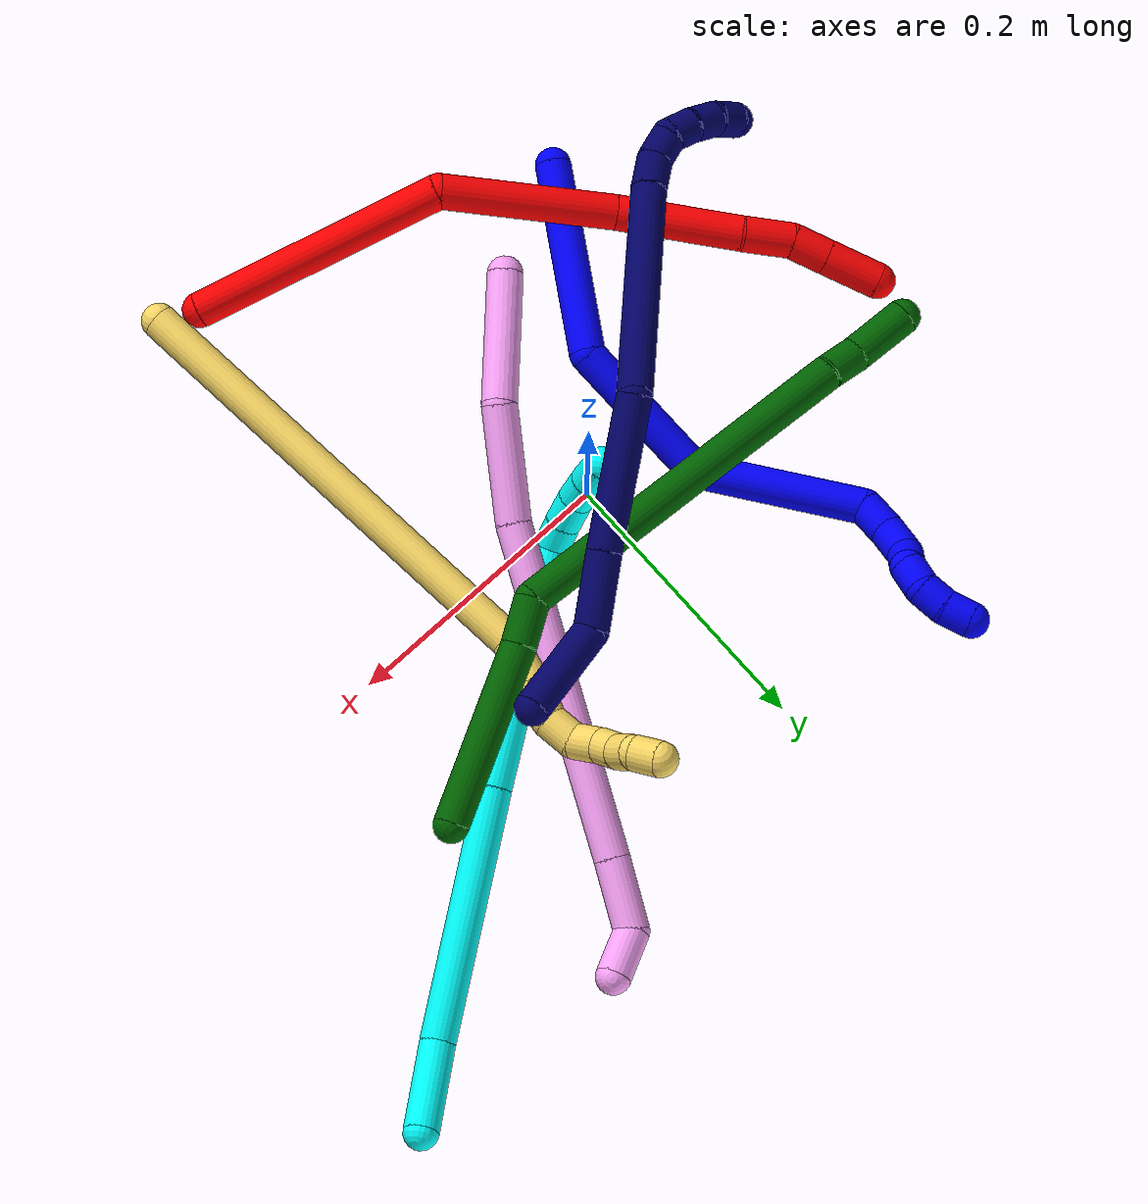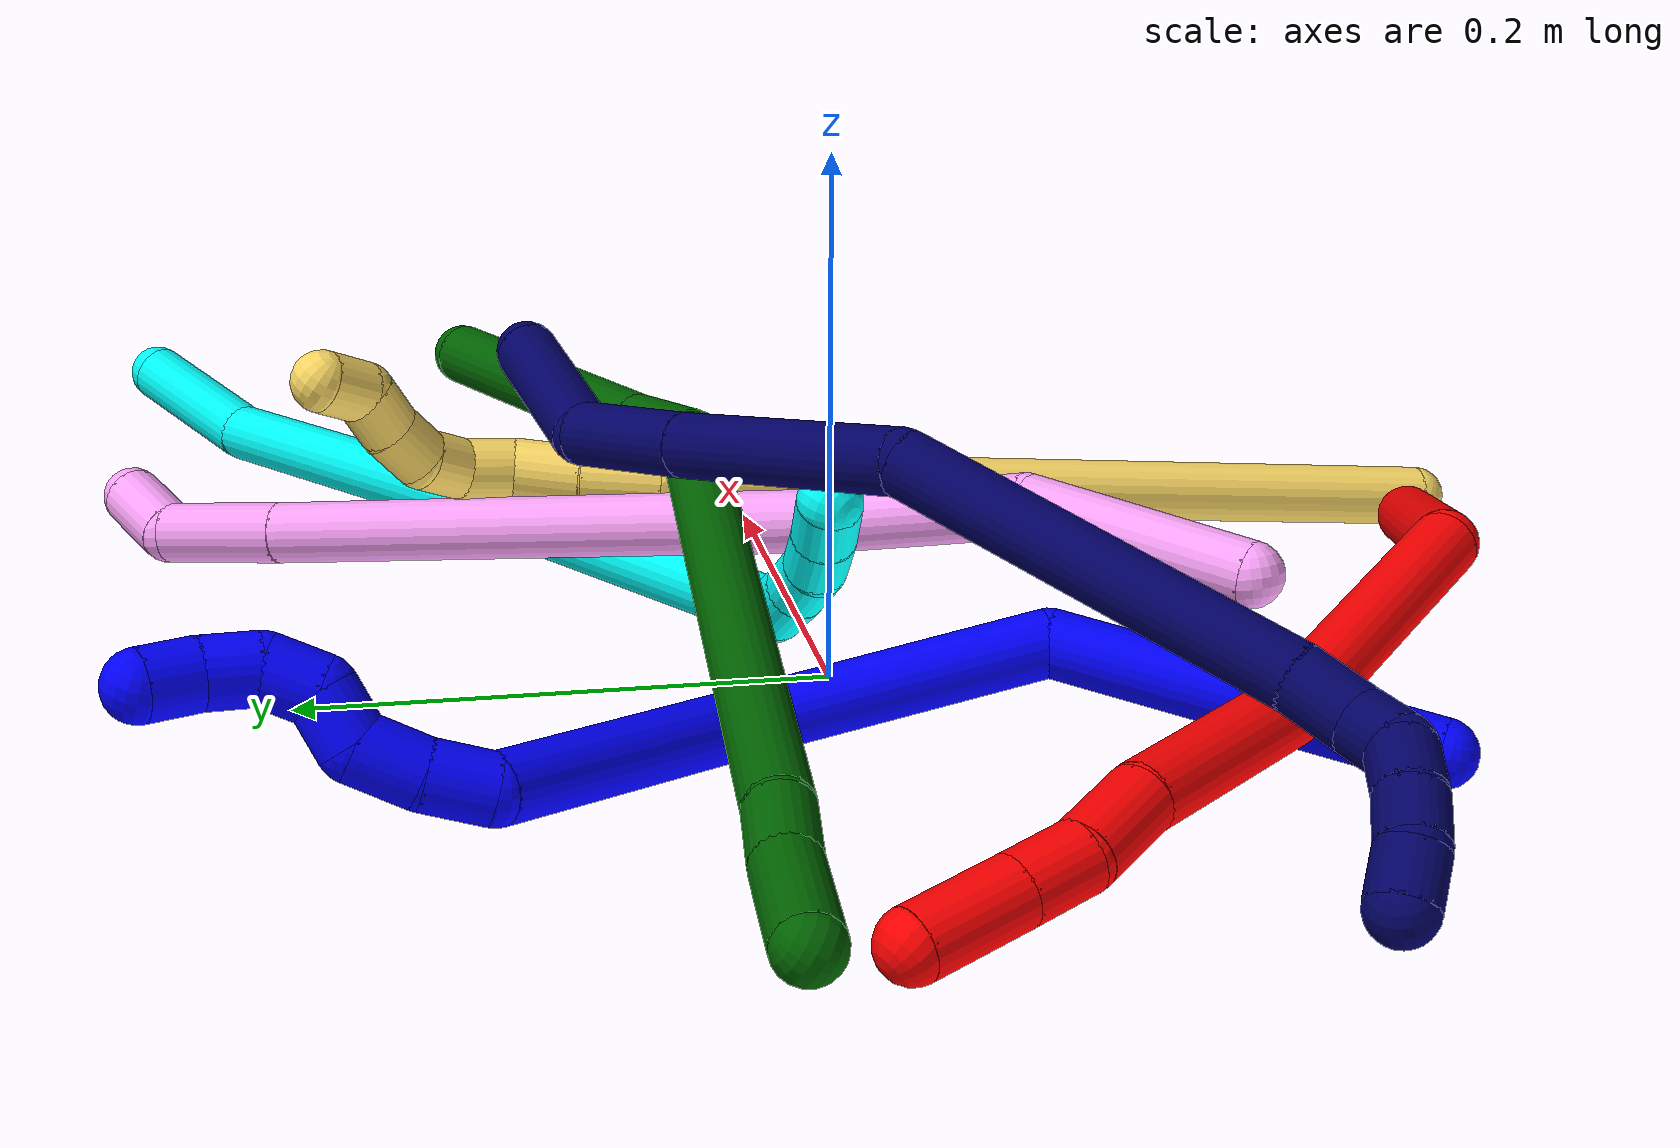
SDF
<sdf version="1.7">
 <world name="default">
  <plugin name="TubeGeneratorPlugin" filename="libtube_generator_plugin.so"/>
  <model name="photoneo_s_sensor">
   <static>1</static>
   <pose>0 0 2 1.57079 1.57079 3.14159</pose>
   <link name="link">
    <inertial><mass>0.1</mass></inertial>
    <sensor name="sensor" type="depth">
     <update_rate>30</update_rate>
     <camera>
      <horizontal_fov>1.22</horizontal_fov>
      <image><width>1920</width><height>1200</height><format>B8G8R8</format></image>
      <clip><near>0.1</near><far>4</far></clip>
      <depth_camera><output>points</output></depth_camera>
     </camera>
     <plugin name="camera_plugin" filename="libgazebo_ros_depth_camera.so">
      <baseline>0.2</baseline>
      <alwaysOn>1</alwaysOn>
      <updateRate>0.0</updateRate>
      <cameraName>camera_ir</cameraName>
      <imageTopicName>/camera/color/image_raw</imageTopicName>
      <cameraInfoTopicName>/camera/color/camera_info</cameraInfoTopicName>
      <depthImageTopicName>/camera/depth/image_raw</depthImageTopicName>
      <depthImageCameraInfoTopicName>/camera/depth/camera_info</depthImageCameraInfoTopicName>
      <pointCloudTopicName>/camera/depth/points</pointCloudTopicName>
      <frameName>fr_optical</frameName>
      <pointCloudCutoff>0.1</pointCloudCutoff>
      <pointCloudCutoffMax>2.0</pointCloudCutoffMax>
      <distortionK1>0</distortionK1>
      <distortionK2>0</distortionK2>
      <distortionK3>0</distortionK3>
      <distortionT1>0</distortionT1>
      <distortionT2>0</distortionT2>
      <CxPrime>0</CxPrime>
      <Cx>0</Cx>
      <Cy>0</Cy>
      <focalLength>0</focalLength>
      <hackBaseline>0</hackBaseline>
     </plugin>
    </sensor>
   </link>
  </model>
  <gravity>0 0 -9.8</gravity>
  <magnetic_field>6e-06 2.3e-05 -4.2e-05</magnetic_field>
  <atmosphere type="adiabatic"/>
  <physics name="default_physics" default="0" type="ode">
   <max_step_size>0.003</max_step_size>
   <real_time_factor>1</real_time_factor>
   <real_time_update_rate>1000</real_time_update_rate>
   <max_contacts>10000</max_contacts>
   <ode>
    <solver>
     <type>quick</type>
     <iters>100</iters>
     <sor>1.3</sor>
     <use_dynamic_moi_rescaling>0</use_dynamic_moi_rescaling>
    </solver>
    <constraints>
     <contact_max_correcting_vel>0</contact_max_correcting_vel>
     <contact_surface_layer>0.001</contact_surface_layer>
     <cfm>0</cfm>
     <erp>0.2</erp>
    </constraints>
   </ode>
  </physics>
  <scene><ambient>0.4 0.4 0.4 1</ambient><background>0.7 0.7 0.7 1</background><shadows>0</shadows></scene>
  <audio><device>default</device></audio>
  <spherical_coordinates>
   <surface_model>EARTH_WGS84</surface_model>
   <latitude_deg>0</latitude_deg>
   <longitude_deg>0</longitude_deg>
   <elevation>0</elevation>
   <heading_deg>0</heading_deg>
  </spherical_coordinates>
  <model name="bin">
   <static>1</static>
   <link name="bottom">
    <collision name="collision-bottom">
     <pose>0 0 -0.01 0 -0 0</pose>
     <geometry><box><size>0.8 0.6 0.02</size></box></geometry>
     <surface>
      <friction><ode><mu>100</mu><mu2>100</mu2></ode></friction>
      <contact><collide_bitmask>65535</collide_bitmask></contact>
     </surface>
    </collision>
   </link>
   <link name="west_wall">
    <collision name="collision-west_wall">
     <pose>-0.41 0 0.1 0 -0 0</pose>
     <geometry><box><size>0.02 0.6 0.2</size></box></geometry>
     <surface>
      <friction><ode><mu>100</mu><mu2>100</mu2></ode></friction>
      <contact><collide_bitmask>65535</collide_bitmask></contact>
     </surface>
    </collision>
   </link>
   <link name="east_wall">
    <collision name="collision-east_wall">
     <pose>0.41 0 0.1 0 -0 0</pose>
     <geometry><box><size>0.02 0.6 0.2</size></box></geometry>
     <surface>
      <friction><ode><mu>100</mu><mu2>100</mu2></ode></friction>
      <contact><collide_bitmask>65535</collide_bitmask></contact>
     </surface>
    </collision>
   </link>
   <link name="south_wall">
    <collision name="collision-south_wall">
     <pose>0 -0.31 0.1 0 -0 0</pose>
     <geometry><box><size>0.8 0.02 0.2</size></box></geometry>
     <surface>
      <friction><ode><mu>100</mu><mu2>100</mu2></ode></friction>
      <contact><collide_bitmask>65535</collide_bitmask></contact>
     </surface>
    </collision>
   </link>
   <link name="north_wall">
    <collision name="collision-north_wall">
     <pose>0 0.31 0.1 0 -0 0</pose>
     <geometry><box><size>0.8 0.02 0.2</size></box></geometry>
     <surface>
      <friction><ode><mu>100</mu><mu2>100</mu2></ode></friction>
      <contact><collide_bitmask>65535</collide_bitmask></contact>
     </surface>
    </collision>
   </link>
  </model>
  <model name="1">
   <static>0</static>
   <link name="1">
    <collision name="collision-cylinder-e_1_1_4">
     <pose>0.03858 0.059249 -0.010072 -1.73918 0.570685 -0.668755</pose>
     <geometry><cylinder><radius>0.0125</radius><length>0.142832</length></cylinder></geometry>
     <surface>
      <friction><ode><mu>1.16</mu><mu2>1.16</mu2><slip1>0</slip1><slip2>0</slip2></ode></friction>
      <contact><ode><kp>1e+06</kp><kd>1</kd><max_vel>0</max_vel><min_depth>0.001</min_depth></ode></contact>
     </surface>
    </collision>
    <visual name="visual-cylinder-e_1_1_4">
     <pose>0.03858 0.059249 -0.010072 -1.73918 0.570685 -0.668755</pose>
     <geometry><cylinder><radius>0.0125</radius><length>0.142832</length></cylinder></geometry>
     <material><ambient>0 0 1 1</ambient></material>
    </visual>
    <collision name="collision-cylinder-e_2_4_5">
     <pose>0.073314 0.167824 -0.041856 -1.98546 -0.071234 0.109124</pose>
     <geometry><cylinder><radius>0.0125</radius><length>0.108061</length></cylinder></geometry>
     <surface>
      <friction><ode><mu>1.16</mu><mu2>1.16</mu2><slip1>0</slip1><slip2>0</slip2></ode></friction>
      <contact><ode><kp>1e+06</kp><kd>1</kd><max_vel>0</max_vel><min_depth>0.001</min_depth></ode></contact>
     </surface>
    </collision>
    <visual name="visual-cylinder-e_2_4_5">
     <pose>0.073314 0.167824 -0.041856 -1.98546 -0.071234 0.109124</pose>
     <geometry><cylinder><radius>0.0125</radius><length>0.108061</length></cylinder></geometry>
     <material><ambient>0 0 1 1</ambient></material>
    </visual>
    <collision name="collision-cylinder-e_3_5_6">
     <pose>0.036352 0.267086 -0.064989 -1.59923 -0.585385 0.601286</pose>
     <geometry><cylinder><radius>0.0125</radius><length>0.119873</length></cylinder></geometry>
     <surface>
      <friction><ode><mu>1.16</mu><mu2>1.16</mu2><slip1>0</slip1><slip2>0</slip2></ode></friction>
      <contact><ode><kp>1e+06</kp><kd>1</kd><max_vel>0</max_vel><min_depth>0.001</min_depth></ode></contact>
     </surface>
    </collision>
    <visual name="visual-cylinder-e_3_5_6">
     <pose>0.036352 0.267086 -0.064989 -1.59923 -0.585385 0.601286</pose>
     <geometry><cylinder><radius>0.0125</radius><length>0.119873</length></cylinder></geometry>
     <material><ambient>0 0 1 1</ambient></material>
    </visual>
    <collision name="collision-cylinder-e_4_6_7">
     <pose>0.004294 0.329026 -0.065985 -1.53545 0.087856 -0.084808</pose>
     <geometry><cylinder><radius>0.0125</radius><length>0.024114</length></cylinder></geometry>
     <surface>
      <friction><ode><mu>1.16</mu><mu2>1.16</mu2><slip1>0</slip1><slip2>0</slip2></ode></friction>
      <contact><ode><kp>1e+06</kp><kd>1</kd><max_vel>0</max_vel><min_depth>0.001</min_depth></ode></contact>
     </surface>
    </collision>
    <visual name="visual-cylinder-e_4_6_7">
     <pose>0.004294 0.329026 -0.065985 -1.53545 0.087856 -0.084808</pose>
     <geometry><cylinder><radius>0.0125</radius><length>0.024114</length></cylinder></geometry>
     <material><ambient>0 0 1 1</ambient></material>
    </visual>
    <collision name="collision-cylinder-e_5_7_8">
     <pose>0.007818 0.352683 -0.063542 -1.39923 0.205559 -0.173183</pose>
     <geometry><cylinder><radius>0.0125</radius><length>0.024163</length></cylinder></geometry>
     <surface>
      <friction><ode><mu>1.16</mu><mu2>1.16</mu2><slip1>0</slip1><slip2>0</slip2></ode></friction>
      <contact><ode><kp>1e+06</kp><kd>1</kd><max_vel>0</max_vel><min_depth>0.001</min_depth></ode></contact>
     </surface>
    </collision>
    <visual name="visual-cylinder-e_5_7_8">
     <pose>0.007818 0.352683 -0.063542 -1.39923 0.205559 -0.173183</pose>
     <geometry><cylinder><radius>0.0125</radius><length>0.024163</length></cylinder></geometry>
     <material><ambient>0 0 1 1</ambient></material>
    </visual>
    <collision name="collision-cylinder-e_6_8_9">
     <pose>0.015301 0.370612 -0.055223 -0.783511 0.513722 -0.216171</pose>
     <geometry><cylinder><radius>0.0125</radius><length>0.02042</length></cylinder></geometry>
     <surface>
      <friction><ode><mu>1.16</mu><mu2>1.16</mu2><slip1>0</slip1><slip2>0</slip2></ode></friction>
      <contact><ode><kp>1e+06</kp><kd>1</kd><max_vel>0</max_vel><min_depth>0.001</min_depth></ode></contact>
     </surface>
    </collision>
    <visual name="visual-cylinder-e_6_8_9">
     <pose>0.015301 0.370612 -0.055223 -0.783511 0.513722 -0.216171</pose>
     <geometry><cylinder><radius>0.0125</radius><length>0.02042</length></cylinder></geometry>
     <material><ambient>0 0 1 1</ambient></material>
    </visual>
    <collision name="collision-cylinder-e_7_9_10">
     <pose>0.022918 0.386686 -0.04778 -1.45462 0.257658 -0.229601</pose>
     <geometry><cylinder><radius>0.0125</radius><length>0.020403</length></cylinder></geometry>
     <surface>
      <friction><ode><mu>1.16</mu><mu2>1.16</mu2><slip1>0</slip1><slip2>0</slip2></ode></friction>
      <contact><ode><kp>1e+06</kp><kd>1</kd><max_vel>0</max_vel><min_depth>0.001</min_depth></ode></contact>
     </surface>
    </collision>
    <visual name="visual-cylinder-e_7_9_10">
     <pose>0.022918 0.386686 -0.04778 -1.45462 0.257658 -0.229601</pose>
     <geometry><cylinder><radius>0.0125</radius><length>0.020403</length></cylinder></geometry>
     <material><ambient>0 0 1 1</ambient></material>
    </visual>
    <collision name="collision-cylinder-e_8_10_11">
     <pose>0.02429 0.406234 -0.048506 -1.7602 -0.122978 0.148705</pose>
     <geometry><cylinder><radius>0.0125</radius><length>0.020006</length></cylinder></geometry>
     <surface>
      <friction><ode><mu>1.16</mu><mu2>1.16</mu2><slip1>0</slip1><slip2>0</slip2></ode></friction>
      <contact><ode><kp>1e+06</kp><kd>1</kd><max_vel>0</max_vel><min_depth>0.001</min_depth></ode></contact>
     </surface>
    </collision>
    <visual name="visual-cylinder-e_8_10_11">
     <pose>0.02429 0.406234 -0.048506 -1.7602 -0.122978 0.148705</pose>
     <geometry><cylinder><radius>0.0125</radius><length>0.020006</length></cylinder></geometry>
     <material><ambient>0 0 1 1</ambient></material>
    </visual>
    <collision name="collision-cylinder-e_9_11_2">
     <pose>0.019365 0.425211 -0.051946 -1.73952 -0.376262 0.443686</pose>
     <geometry><cylinder><radius>0.0125</radius><length>0.020129</length></cylinder></geometry>
     <surface>
      <friction><ode><mu>1.16</mu><mu2>1.16</mu2><slip1>0</slip1><slip2>0</slip2></ode></friction>
      <contact><ode><kp>1e+06</kp><kd>1</kd><max_vel>0</max_vel><min_depth>0.001</min_depth></ode></contact>
     </surface>
    </collision>
    <visual name="visual-cylinder-e_9_11_2">
     <pose>0.019365 0.425211 -0.051946 -1.73952 -0.376262 0.443686</pose>
     <geometry><cylinder><radius>0.0125</radius><length>0.020129</length></cylinder></geometry>
     <material><ambient>0 0 1 1</ambient></material>
    </visual>
    <collision name="collision-sphere-2">
     <pose>0.015667 0.434439 -0.053518 0 -0 0</pose>
     <geometry><sphere><radius>0.0125</radius></sphere></geometry>
     <surface>
      <friction><ode><mu>1.16</mu><mu2>1.16</mu2><slip1>0</slip1><slip2>0</slip2></ode></friction>
      <contact><ode><kp>1e+06</kp><kd>1</kd><max_vel>0</max_vel><min_depth>0.001</min_depth></ode></contact>
     </surface>
    </collision>
    <visual name="visual-sphere-2">
     <pose>0.015667 0.434439 -0.053518 0 -0 0</pose>
     <geometry><sphere><radius>0.0125</radius></sphere></geometry>
     <material><ambient>0 0 1 1</ambient></material>
    </visual>
    <collision name="collision-sphere-11">
     <pose>0.023063 0.415984 -0.050375 0 -0 0</pose>
     <geometry><sphere><radius>0.0125</radius></sphere></geometry>
     <surface>
      <friction><ode><mu>1.16</mu><mu2>1.16</mu2><slip1>0</slip1><slip2>0</slip2></ode></friction>
      <contact><ode><kp>1e+06</kp><kd>1</kd><max_vel>0</max_vel><min_depth>0.001</min_depth></ode></contact>
     </surface>
    </collision>
    <visual name="visual-sphere-11">
     <pose>0.023063 0.415984 -0.050375 0 -0 0</pose>
     <geometry><sphere><radius>0.0125</radius></sphere></geometry>
     <material><ambient>0 0 1 1</ambient></material>
    </visual>
    <collision name="collision-sphere-10">
     <pose>0.025517 0.396484 -0.046637 0 -0 0</pose>
     <geometry><sphere><radius>0.0125</radius></sphere></geometry>
     <surface>
      <friction><ode><mu>1.16</mu><mu2>1.16</mu2><slip1>0</slip1><slip2>0</slip2></ode></friction>
      <contact><ode><kp>1e+06</kp><kd>1</kd><max_vel>0</max_vel><min_depth>0.001</min_depth></ode></contact>
     </surface>
    </collision>
    <visual name="visual-sphere-10">
     <pose>0.025517 0.396484 -0.046637 0 -0 0</pose>
     <geometry><sphere><radius>0.0125</radius></sphere></geometry>
     <material><ambient>0 0 1 1</ambient></material>
    </visual>
    <collision name="collision-sphere-9">
     <pose>0.020318 0.376888 -0.048923 0 -0 0</pose>
     <geometry><sphere><radius>0.0125</radius></sphere></geometry>
     <surface>
      <friction><ode><mu>1.16</mu><mu2>1.16</mu2><slip1>0</slip1><slip2>0</slip2></ode></friction>
      <contact><ode><kp>1e+06</kp><kd>1</kd><max_vel>0</max_vel><min_depth>0.001</min_depth></ode></contact>
     </surface>
    </collision>
    <visual name="visual-sphere-9">
     <pose>0.020318 0.376888 -0.048923 0 -0 0</pose>
     <geometry><sphere><radius>0.0125</radius></sphere></geometry>
     <material><ambient>0 0 1 1</ambient></material>
    </visual>
    <collision name="collision-sphere-4">
     <pose>0.077159 0.118498 -0.020144 0 -0 0</pose>
     <geometry><sphere><radius>0.0125</radius></sphere></geometry>
     <surface>
      <friction><ode><mu>1.16</mu><mu2>1.16</mu2><slip1>0</slip1><slip2>0</slip2></ode></friction>
      <contact><ode><kp>1e+06</kp><kd>1</kd><max_vel>0</max_vel><min_depth>0.001</min_depth></ode></contact>
     </surface>
    </collision>
    <visual name="visual-sphere-4">
     <pose>0.077159 0.118498 -0.020144 0 -0 0</pose>
     <geometry><sphere><radius>0.0125</radius></sphere></geometry>
     <material><ambient>0 0 1 1</ambient></material>
    </visual>
    <collision name="collision-sphere-1">
     <geometry><sphere><radius>0.0125</radius></sphere></geometry>
     <surface>
      <friction><ode><mu>1.16</mu><mu2>1.16</mu2><slip1>0</slip1><slip2>0</slip2></ode></friction>
      <contact><ode><kp>1e+06</kp><kd>1</kd><max_vel>0</max_vel><min_depth>0.001</min_depth></ode></contact>
     </surface>
    </collision>
    <visual name="visual-sphere-1">
     <geometry><sphere><radius>0.0125</radius></sphere></geometry>
     <material><ambient>0 0 1 1</ambient></material>
    </visual>
    <collision name="collision-sphere-8">
     <pose>0.010284 0.364336 -0.061522 0 -0 0</pose>
     <geometry><sphere><radius>0.0125</radius></sphere></geometry>
     <surface>
      <friction><ode><mu>1.16</mu><mu2>1.16</mu2><slip1>0</slip1><slip2>0</slip2></ode></friction>
      <contact><ode><kp>1e+06</kp><kd>1</kd><max_vel>0</max_vel><min_depth>0.001</min_depth></ode></contact>
     </surface>
    </collision>
    <visual name="visual-sphere-8">
     <pose>0.010284 0.364336 -0.061522 0 -0 0</pose>
     <geometry><sphere><radius>0.0125</radius></sphere></geometry>
     <material><ambient>0 0 1 1</ambient></material>
    </visual>
    <collision name="collision-sphere-5">
     <pose>0.069468 0.21715 -0.063569 0 -0 0</pose>
     <geometry><sphere><radius>0.0125</radius></sphere></geometry>
     <surface>
      <friction><ode><mu>1.16</mu><mu2>1.16</mu2><slip1>0</slip1><slip2>0</slip2></ode></friction>
      <contact><ode><kp>1e+06</kp><kd>1</kd><max_vel>0</max_vel><min_depth>0.001</min_depth></ode></contact>
     </surface>
    </collision>
    <visual name="visual-sphere-5">
     <pose>0.069468 0.21715 -0.063569 0 -0 0</pose>
     <geometry><sphere><radius>0.0125</radius></sphere></geometry>
     <material><ambient>0 0 1 1</ambient></material>
    </visual>
    <collision name="collision-sphere-6">
     <pose>0.003236 0.317023 -0.06641 0 -0 0</pose>
     <geometry><sphere><radius>0.0125</radius></sphere></geometry>
     <surface>
      <friction><ode><mu>1.16</mu><mu2>1.16</mu2><slip1>0</slip1><slip2>0</slip2></ode></friction>
      <contact><ode><kp>1e+06</kp><kd>1</kd><max_vel>0</max_vel><min_depth>0.001</min_depth></ode></contact>
     </surface>
    </collision>
    <visual name="visual-sphere-6">
     <pose>0.003236 0.317023 -0.06641 0 -0 0</pose>
     <geometry><sphere><radius>0.0125</radius></sphere></geometry>
     <material><ambient>0 0 1 1</ambient></material>
    </visual>
    <collision name="collision-sphere-7">
     <pose>0.005352 0.341029 -0.065561 0 -0 0</pose>
     <geometry><sphere><radius>0.0125</radius></sphere></geometry>
     <surface>
      <friction><ode><mu>1.16</mu><mu2>1.16</mu2><slip1>0</slip1><slip2>0</slip2></ode></friction>
      <contact><ode><kp>1e+06</kp><kd>1</kd><max_vel>0</max_vel><min_depth>0.001</min_depth></ode></contact>
     </surface>
    </collision>
    <visual name="visual-sphere-7">
     <pose>0.005352 0.341029 -0.065561 0 -0 0</pose>
     <geometry><sphere><radius>0.0125</radius></sphere></geometry>
     <material><ambient>0 0 1 1</ambient></material>
    </visual>
    <inertial>
     <pose>0.039477 0.214427 -0.041994 0 -0 0</pose>
     <mass>0.5</mass>
     <inertia>
      <ixx>0.000337</ixx>
      <ixy>0</ixy>
      <ixz>0</ixz>
      <iyy>3.7e-05</iyy>
      <iyz>0</iyz>
      <izz>-0.000488</izz>
     </inertia>
    </inertial>
   </link>
   <pose>-0.136186 -0.18809 0.011496 0.233326 -0.165967 -0.002882</pose>
  </model>
  <model name="2">
   <static>0</static>
   <link name="2">
    <collision name="collision-cylinder-e_1_1_4">
     <pose>-0.068712 0.053725 -0.033004 -2.12168 -0.828323 1.33224</pose>
     <geometry><cylinder><radius>0.0125</radius><length>0.186516</length></cylinder></geometry>
     <surface>
      <friction><ode><mu>1.16</mu><mu2>1.16</mu2><slip1>0</slip1><slip2>0</slip2></ode></friction>
      <contact><ode><kp>1e+06</kp><kd>1</kd><max_vel>0</max_vel><min_depth>0.001</min_depth></ode></contact>
     </surface>
    </collision>
    <visual name="visual-cylinder-e_1_1_4">
     <pose>-0.068712 0.053725 -0.033004 -2.12168 -0.828323 1.33224</pose>
     <geometry><cylinder><radius>0.0125</radius><length>0.186516</length></cylinder></geometry>
     <material><ambient>1 0 0 1</ambient></material>
    </visual>
    <collision name="collision-cylinder-e_2_4_5">
     <pose>-0.16072 0.130274 -0.119077 -2.73542 -0.383307 1.51135</pose>
     <geometry><cylinder><radius>0.0125</radius><length>0.124577</length></cylinder></geometry>
     <surface>
      <friction><ode><mu>1.16</mu><mu2>1.16</mu2><slip1>0</slip1><slip2>0</slip2></ode></friction>
      <contact><ode><kp>1e+06</kp><kd>1</kd><max_vel>0</max_vel><min_depth>0.001</min_depth></ode></contact>
     </surface>
    </collision>
    <visual name="visual-cylinder-e_2_4_5">
     <pose>-0.16072 0.130274 -0.119077 -2.73542 -0.383307 1.51135</pose>
     <geometry><cylinder><radius>0.0125</radius><length>0.124577</length></cylinder></geometry>
     <material><ambient>1 0 0 1</ambient></material>
    </visual>
    <collision name="collision-cylinder-e_3_5_6">
     <pose>-0.19691 0.176327 -0.207307 -2.55779 -0.296939 0.923713</pose>
     <geometry><cylinder><radius>0.0125</radius><length>0.088142</length></cylinder></geometry>
     <surface>
      <friction><ode><mu>1.16</mu><mu2>1.16</mu2><slip1>0</slip1><slip2>0</slip2></ode></friction>
      <contact><ode><kp>1e+06</kp><kd>1</kd><max_vel>0</max_vel><min_depth>0.001</min_depth></ode></contact>
     </surface>
    </collision>
    <visual name="visual-cylinder-e_3_5_6">
     <pose>-0.19691 0.176327 -0.207307 -2.55779 -0.296939 0.923713</pose>
     <geometry><cylinder><radius>0.0125</radius><length>0.088142</length></cylinder></geometry>
     <material><ambient>1 0 0 1</ambient></material>
    </visual>
    <collision name="collision-cylinder-e_4_6_7">
     <pose>-0.21597 0.206114 -0.257503 -2.73023 -0.359576 1.43329</pose>
     <geometry><cylinder><radius>0.0125</radius><length>0.035043</length></cylinder></geometry>
     <surface>
      <friction><ode><mu>1.16</mu><mu2>1.16</mu2><slip1>0</slip1><slip2>0</slip2></ode></friction>
      <contact><ode><kp>1e+06</kp><kd>1</kd><max_vel>0</max_vel><min_depth>0.001</min_depth></ode></contact>
     </surface>
    </collision>
    <visual name="visual-cylinder-e_4_6_7">
     <pose>-0.21597 0.206114 -0.257503 -2.73023 -0.359576 1.43329</pose>
     <geometry><cylinder><radius>0.0125</radius><length>0.035043</length></cylinder></geometry>
     <material><ambient>1 0 0 1</ambient></material>
    </visual>
    <collision name="collision-cylinder-e_5_7_8">
     <pose>-0.222824 0.218227 -0.284412 -2.70415 -0.052479 0.235063</pose>
     <geometry><cylinder><radius>0.0125</radius><length>0.026258</length></cylinder></geometry>
     <surface>
      <friction><ode><mu>1.16</mu><mu2>1.16</mu2><slip1>0</slip1><slip2>0</slip2></ode></friction>
      <contact><ode><kp>1e+06</kp><kd>1</kd><max_vel>0</max_vel><min_depth>0.001</min_depth></ode></contact>
     </surface>
    </collision>
    <visual name="visual-cylinder-e_5_7_8">
     <pose>-0.222824 0.218227 -0.284412 -2.70415 -0.052479 0.235063</pose>
     <geometry><cylinder><radius>0.0125</radius><length>0.026258</length></cylinder></geometry>
     <material><ambient>1 0 0 1</ambient></material>
    </visual>
    <collision name="collision-cylinder-e_6_8_2">
     <pose>-0.224581 0.23233 -0.31404 -2.69279 -0.054157 0.23623</pose>
     <geometry><cylinder><radius>0.0125</radius><length>0.039464</length></cylinder></geometry>
     <surface>
      <friction><ode><mu>1.16</mu><mu2>1.16</mu2><slip1>0</slip1><slip2>0</slip2></ode></friction>
      <contact><ode><kp>1e+06</kp><kd>1</kd><max_vel>0</max_vel><min_depth>0.001</min_depth></ode></contact>
     </surface>
    </collision>
    <visual name="visual-cylinder-e_6_8_2">
     <pose>-0.224581 0.23233 -0.31404 -2.69279 -0.054157 0.23623</pose>
     <geometry><cylinder><radius>0.0125</radius><length>0.039464</length></cylinder></geometry>
     <material><ambient>1 0 0 1</ambient></material>
    </visual>
    <collision name="collision-sphere-2">
     <pose>-0.225649 0.240878 -0.331792 0 -0 0</pose>
     <geometry><sphere><radius>0.0125</radius></sphere></geometry>
     <surface>
      <friction><ode><mu>1.16</mu><mu2>1.16</mu2><slip1>0</slip1><slip2>0</slip2></ode></friction>
      <contact><ode><kp>1e+06</kp><kd>1</kd><max_vel>0</max_vel><min_depth>0.001</min_depth></ode></contact>
     </surface>
    </collision>
    <visual name="visual-sphere-2">
     <pose>-0.225649 0.240878 -0.331792 0 -0 0</pose>
     <geometry><sphere><radius>0.0125</radius></sphere></geometry>
     <material><ambient>1 0 0 1</ambient></material>
    </visual>
    <collision name="collision-sphere-4">
     <pose>-0.137424 0.10745 -0.066008 0 -0 0</pose>
     <geometry><sphere><radius>0.0125</radius></sphere></geometry>
     <surface>
      <friction><ode><mu>1.16</mu><mu2>1.16</mu2><slip1>0</slip1><slip2>0</slip2></ode></friction>
      <contact><ode><kp>1e+06</kp><kd>1</kd><max_vel>0</max_vel><min_depth>0.001</min_depth></ode></contact>
     </surface>
    </collision>
    <visual name="visual-sphere-4">
     <pose>-0.137424 0.10745 -0.066008 0 -0 0</pose>
     <geometry><sphere><radius>0.0125</radius></sphere></geometry>
     <material><ambient>1 0 0 1</ambient></material>
    </visual>
    <collision name="collision-sphere-1">
     <geometry><sphere><radius>0.0125</radius></sphere></geometry>
     <surface>
      <friction><ode><mu>1.16</mu><mu2>1.16</mu2><slip1>0</slip1><slip2>0</slip2></ode></friction>
      <contact><ode><kp>1e+06</kp><kd>1</kd><max_vel>0</max_vel><min_depth>0.001</min_depth></ode></contact>
     </surface>
    </collision>
    <visual name="visual-sphere-1">
     <geometry><sphere><radius>0.0125</radius></sphere></geometry>
     <material><ambient>1 0 0 1</ambient></material>
    </visual>
    <collision name="collision-sphere-8">
     <pose>-0.223513 0.223781 -0.296289 0 -0 0</pose>
     <geometry><sphere><radius>0.0125</radius></sphere></geometry>
     <surface>
      <friction><ode><mu>1.16</mu><mu2>1.16</mu2><slip1>0</slip1><slip2>0</slip2></ode></friction>
      <contact><ode><kp>1e+06</kp><kd>1</kd><max_vel>0</max_vel><min_depth>0.001</min_depth></ode></contact>
     </surface>
    </collision>
    <visual name="visual-sphere-8">
     <pose>-0.223513 0.223781 -0.296289 0 -0 0</pose>
     <geometry><sphere><radius>0.0125</radius></sphere></geometry>
     <material><ambient>1 0 0 1</ambient></material>
    </visual>
    <collision name="collision-sphere-5">
     <pose>-0.184015 0.153098 -0.172145 0 -0 0</pose>
     <geometry><sphere><radius>0.0125</radius></sphere></geometry>
     <surface>
      <friction><ode><mu>1.16</mu><mu2>1.16</mu2><slip1>0</slip1><slip2>0</slip2></ode></friction>
      <contact><ode><kp>1e+06</kp><kd>1</kd><max_vel>0</max_vel><min_depth>0.001</min_depth></ode></contact>
     </surface>
    </collision>
    <visual name="visual-sphere-5">
     <pose>-0.184015 0.153098 -0.172145 0 -0 0</pose>
     <geometry><sphere><radius>0.0125</radius></sphere></geometry>
     <material><ambient>1 0 0 1</ambient></material>
    </visual>
    <collision name="collision-sphere-6">
     <pose>-0.209805 0.199556 -0.24247 0 -0 0</pose>
     <geometry><sphere><radius>0.0125</radius></sphere></geometry>
     <surface>
      <friction><ode><mu>1.16</mu><mu2>1.16</mu2><slip1>0</slip1><slip2>0</slip2></ode></friction>
      <contact><ode><kp>1e+06</kp><kd>1</kd><max_vel>0</max_vel><min_depth>0.001</min_depth></ode></contact>
     </surface>
    </collision>
    <visual name="visual-sphere-6">
     <pose>-0.209805 0.199556 -0.24247 0 -0 0</pose>
     <geometry><sphere><radius>0.0125</radius></sphere></geometry>
     <material><ambient>1 0 0 1</ambient></material>
    </visual>
    <collision name="collision-sphere-7">
     <pose>-0.222136 0.212673 -0.272536 0 -0 0</pose>
     <geometry><sphere><radius>0.0125</radius></sphere></geometry>
     <surface>
      <friction><ode><mu>1.16</mu><mu2>1.16</mu2><slip1>0</slip1><slip2>0</slip2></ode></friction>
      <contact><ode><kp>1e+06</kp><kd>1</kd><max_vel>0</max_vel><min_depth>0.001</min_depth></ode></contact>
     </surface>
    </collision>
    <visual name="visual-sphere-7">
     <pose>-0.222136 0.212673 -0.272536 0 -0 0</pose>
     <geometry><sphere><radius>0.0125</radius></sphere></geometry>
     <material><ambient>1 0 0 1</ambient></material>
    </visual>
    <inertial>
     <pose>-0.144952 0.127827 -0.136295 0 -0 0</pose>
     <mass>0.5</mass>
     <inertia><ixx>0.00069</ixx><ixy>0</ixy><ixz>0</ixz><iyy>0.000837</iyy><iyz>0</iyz><izz>4.6e-05</izz></inertia>
    </inertial>
   </link>
   <pose>0.114282 -0.273305 0.012436 0.946328 -0.010487 0.384097</pose>
  </model>
  <model name="3">
   <static>0</static>
   <link name="3">
    <collision name="collision-cylinder-e_1_1_4">
     <pose>0.001126 -0.000221 -0.032635 3.13482 0.034484 2.75353</pose>
     <geometry><cylinder><radius>0.0125</radius><length>0.06531</length></cylinder></geometry>
     <surface>
      <friction><ode><mu>1.16</mu><mu2>1.16</mu2><slip1>0</slip1><slip2>0</slip2></ode></friction>
      <contact><ode><kp>1e+06</kp><kd>1</kd><max_vel>0</max_vel><min_depth>0.001</min_depth></ode></contact>
     </surface>
    </collision>
    <visual name="visual-cylinder-e_1_1_4">
     <pose>0.001126 -0.000221 -0.032635 3.13482 0.034484 2.75353</pose>
     <geometry><cylinder><radius>0.0125</radius><length>0.06531</length></cylinder></geometry>
     <material><ambient>0.003922 1 0.996078 1</ambient></material>
    </visual>
    <collision name="collision-cylinder-e_2_4_5">
     <pose>-0.01439 -0.017397 -0.151082 2.94652 -0.188007 -1.5337</pose>
     <geometry><cylinder><radius>0.0125</radius><length>0.17808</length></cylinder></geometry>
     <surface>
      <friction><ode><mu>1.16</mu><mu2>1.16</mu2><slip1>0</slip1><slip2>0</slip2></ode></friction>
      <contact><ode><kp>1e+06</kp><kd>1</kd><max_vel>0</max_vel><min_depth>0.001</min_depth></ode></contact>
     </surface>
    </collision>
    <visual name="visual-cylinder-e_2_4_5">
     <pose>-0.01439 -0.017397 -0.151082 2.94652 -0.188007 -1.5337</pose>
     <geometry><cylinder><radius>0.0125</radius><length>0.17808</length></cylinder></geometry>
     <material><ambient>0.003922 1 0.996078 1</ambient></material>
    </visual>
    <collision name="collision-cylinder-e_3_5_6">
     <pose>-0.04649 -0.047829 -0.320648 2.98205 -0.180246 -1.6931</pose>
     <geometry><cylinder><radius>0.0125</radius><length>0.172458</length></cylinder></geometry>
     <surface>
      <friction><ode><mu>1.16</mu><mu2>1.16</mu2><slip1>0</slip1><slip2>0</slip2></ode></friction>
      <contact><ode><kp>1e+06</kp><kd>1</kd><max_vel>0</max_vel><min_depth>0.001</min_depth></ode></contact>
     </surface>
    </collision>
    <visual name="visual-cylinder-e_3_5_6">
     <pose>-0.04649 -0.047829 -0.320648 2.98205 -0.180246 -1.6931</pose>
     <geometry><cylinder><radius>0.0125</radius><length>0.172458</length></cylinder></geometry>
     <material><ambient>0.003922 1 0.996078 1</ambient></material>
    </visual>
    <collision name="collision-cylinder-e_4_6_7">
     <pose>-0.069641 -0.06637 -0.410433 2.44296 -0.77372 -1.68248</pose>
     <geometry><cylinder><radius>0.0125</radius><length>0.022016</length></cylinder></geometry>
     <surface>
      <friction><ode><mu>1.16</mu><mu2>1.16</mu2><slip1>0</slip1><slip2>0</slip2></ode></friction>
      <contact><ode><kp>1e+06</kp><kd>1</kd><max_vel>0</max_vel><min_depth>0.001</min_depth></ode></contact>
     </surface>
    </collision>
    <visual name="visual-cylinder-e_4_6_7">
     <pose>-0.069641 -0.06637 -0.410433 2.44296 -0.77372 -1.68248</pose>
     <geometry><cylinder><radius>0.0125</radius><length>0.022016</length></cylinder></geometry>
     <material><ambient>0.003922 1 0.996078 1</ambient></material>
    </visual>
    <collision name="collision-cylinder-e_5_7_8">
     <pose>-0.08517 -0.075901 -0.421856 2.45 -0.841525 -1.78591</pose>
     <geometry><cylinder><radius>0.0125</radius><length>0.02102</length></cylinder></geometry>
     <surface>
      <friction><ode><mu>1.16</mu><mu2>1.16</mu2><slip1>0</slip1><slip2>0</slip2></ode></friction>
      <contact><ode><kp>1e+06</kp><kd>1</kd><max_vel>0</max_vel><min_depth>0.001</min_depth></ode></contact>
     </surface>
    </collision>
    <visual name="visual-cylinder-e_5_7_8">
     <pose>-0.08517 -0.075901 -0.421856 2.45 -0.841525 -1.78591</pose>
     <geometry><cylinder><radius>0.0125</radius><length>0.02102</length></cylinder></geometry>
     <material><ambient>0.003922 1 0.996078 1</ambient></material>
    </visual>
    <collision name="collision-cylinder-e_6_8_9">
     <pose>-0.101355 -0.085019 -0.430228 2.14024 -0.986315 -1.55285</pose>
     <geometry><cylinder><radius>0.0125</radius><length>0.020018</length></cylinder></geometry>
     <surface>
      <friction><ode><mu>1.16</mu><mu2>1.16</mu2><slip1>0</slip1><slip2>0</slip2></ode></friction>
      <contact><ode><kp>1e+06</kp><kd>1</kd><max_vel>0</max_vel><min_depth>0.001</min_depth></ode></contact>
     </surface>
    </collision>
    <visual name="visual-cylinder-e_6_8_9">
     <pose>-0.101355 -0.085019 -0.430228 2.14024 -0.986315 -1.55285</pose>
     <geometry><cylinder><radius>0.0125</radius><length>0.020018</length></cylinder></geometry>
     <material><ambient>0.003922 1 0.996078 1</ambient></material>
    </visual>
    <collision name="collision-cylinder-e_7_9_2">
     <pose>-0.118826 -0.094314 -0.435749 2.07186 -1.0449 -1.54229</pose>
     <geometry><cylinder><radius>0.0125</radius><length>0.021098</length></cylinder></geometry>
     <surface>
      <friction><ode><mu>1.16</mu><mu2>1.16</mu2><slip1>0</slip1><slip2>0</slip2></ode></friction>
      <contact><ode><kp>1e+06</kp><kd>1</kd><max_vel>0</max_vel><min_depth>0.001</min_depth></ode></contact>
     </surface>
    </collision>
    <visual name="visual-cylinder-e_7_9_2">
     <pose>-0.118826 -0.094314 -0.435749 2.07186 -1.0449 -1.54229</pose>
     <geometry><cylinder><radius>0.0125</radius><length>0.021098</length></cylinder></geometry>
     <material><ambient>0.003922 1 0.996078 1</ambient></material>
    </visual>
    <collision name="collision-sphere-2">
     <pose>-0.127949 -0.098959 -0.438293 0 -0 0</pose>
     <geometry><sphere><radius>0.0125</radius></sphere></geometry>
     <surface>
      <friction><ode><mu>1.16</mu><mu2>1.16</mu2><slip1>0</slip1><slip2>0</slip2></ode></friction>
      <contact><ode><kp>1e+06</kp><kd>1</kd><max_vel>0</max_vel><min_depth>0.001</min_depth></ode></contact>
     </surface>
    </collision>
    <visual name="visual-sphere-2">
     <pose>-0.127949 -0.098959 -0.438293 0 -0 0</pose>
     <geometry><sphere><radius>0.0125</radius></sphere></geometry>
     <material><ambient>0.003922 1 0.996078 1</ambient></material>
    </visual>
    <collision name="collision-sphere-9">
     <pose>-0.109702 -0.08967 -0.433205 0 -0 0</pose>
     <geometry><sphere><radius>0.0125</radius></sphere></geometry>
     <surface>
      <friction><ode><mu>1.16</mu><mu2>1.16</mu2><slip1>0</slip1><slip2>0</slip2></ode></friction>
      <contact><ode><kp>1e+06</kp><kd>1</kd><max_vel>0</max_vel><min_depth>0.001</min_depth></ode></contact>
     </surface>
    </collision>
    <visual name="visual-sphere-9">
     <pose>-0.109702 -0.08967 -0.433205 0 -0 0</pose>
     <geometry><sphere><radius>0.0125</radius></sphere></geometry>
     <material><ambient>0.003922 1 0.996078 1</ambient></material>
    </visual>
    <collision name="collision-sphere-4">
     <pose>0.002252 -0.000442 -0.06527 0 -0 0</pose>
     <geometry><sphere><radius>0.0125</radius></sphere></geometry>
     <surface>
      <friction><ode><mu>1.16</mu><mu2>1.16</mu2><slip1>0</slip1><slip2>0</slip2></ode></friction>
      <contact><ode><kp>1e+06</kp><kd>1</kd><max_vel>0</max_vel><min_depth>0.001</min_depth></ode></contact>
     </surface>
    </collision>
    <visual name="visual-sphere-4">
     <pose>0.002252 -0.000442 -0.06527 0 -0 0</pose>
     <geometry><sphere><radius>0.0125</radius></sphere></geometry>
     <material><ambient>0.003922 1 0.996078 1</ambient></material>
    </visual>
    <collision name="collision-sphere-1">
     <geometry><sphere><radius>0.0125</radius></sphere></geometry>
     <surface>
      <friction><ode><mu>1.16</mu><mu2>1.16</mu2><slip1>0</slip1><slip2>0</slip2></ode></friction>
      <contact><ode><kp>1e+06</kp><kd>1</kd><max_vel>0</max_vel><min_depth>0.001</min_depth></ode></contact>
     </surface>
    </collision>
    <visual name="visual-sphere-1">
     <geometry><sphere><radius>0.0125</radius></sphere></geometry>
     <material><ambient>0.003922 1 0.996078 1</ambient></material>
    </visual>
    <collision name="collision-sphere-8">
     <pose>-0.093007 -0.080367 -0.42725 0 -0 0</pose>
     <geometry><sphere><radius>0.0125</radius></sphere></geometry>
     <surface>
      <friction><ode><mu>1.16</mu><mu2>1.16</mu2><slip1>0</slip1><slip2>0</slip2></ode></friction>
      <contact><ode><kp>1e+06</kp><kd>1</kd><max_vel>0</max_vel><min_depth>0.001</min_depth></ode></contact>
     </surface>
    </collision>
    <visual name="visual-sphere-8">
     <pose>-0.093007 -0.080367 -0.42725 0 -0 0</pose>
     <geometry><sphere><radius>0.0125</radius></sphere></geometry>
     <material><ambient>0.003922 1 0.996078 1</ambient></material>
    </visual>
    <collision name="collision-sphere-5">
     <pose>-0.031032 -0.034352 -0.236893 0 -0 0</pose>
     <geometry><sphere><radius>0.0125</radius></sphere></geometry>
     <surface>
      <friction><ode><mu>1.16</mu><mu2>1.16</mu2><slip1>0</slip1><slip2>0</slip2></ode></friction>
      <contact><ode><kp>1e+06</kp><kd>1</kd><max_vel>0</max_vel><min_depth>0.001</min_depth></ode></contact>
     </surface>
    </collision>
    <visual name="visual-sphere-5">
     <pose>-0.031032 -0.034352 -0.236893 0 -0 0</pose>
     <geometry><sphere><radius>0.0125</radius></sphere></geometry>
     <material><ambient>0.003922 1 0.996078 1</ambient></material>
    </visual>
    <collision name="collision-sphere-6">
     <pose>-0.061948 -0.061306 -0.404403 0 -0 0</pose>
     <geometry><sphere><radius>0.0125</radius></sphere></geometry>
     <surface>
      <friction><ode><mu>1.16</mu><mu2>1.16</mu2><slip1>0</slip1><slip2>0</slip2></ode></friction>
      <contact><ode><kp>1e+06</kp><kd>1</kd><max_vel>0</max_vel><min_depth>0.001</min_depth></ode></contact>
     </surface>
    </collision>
    <visual name="visual-sphere-6">
     <pose>-0.061948 -0.061306 -0.404403 0 -0 0</pose>
     <geometry><sphere><radius>0.0125</radius></sphere></geometry>
     <material><ambient>0.003922 1 0.996078 1</ambient></material>
    </visual>
    <collision name="collision-sphere-7">
     <pose>-0.077333 -0.071435 -0.416462 0 -0 0</pose>
     <geometry><sphere><radius>0.0125</radius></sphere></geometry>
     <surface>
      <friction><ode><mu>1.16</mu><mu2>1.16</mu2><slip1>0</slip1><slip2>0</slip2></ode></friction>
      <contact><ode><kp>1e+06</kp><kd>1</kd><max_vel>0</max_vel><min_depth>0.001</min_depth></ode></contact>
     </surface>
    </collision>
    <visual name="visual-sphere-7">
     <pose>-0.077333 -0.071435 -0.416462 0 -0 0</pose>
     <geometry><sphere><radius>0.0125</radius></sphere></geometry>
     <material><ambient>0.003922 1 0.996078 1</ambient></material>
    </visual>
    <inertial>
     <pose>-0.036732 -0.036219 -0.240087 0 -0 0</pose>
     <mass>0.5</mass>
     <inertia>
      <ixx>-0.000956</ixx>
      <ixy>0</ixy>
      <ixz>0</ixz>
      <iyy>-0.000802</iyy>
      <iyz>0</iyz>
      <izz>0.000299</izz>
     </inertia>
    </inertial>
   </link>
   <pose>0.378762 0.2563 0.029261 -1.23728 0.692377 -0.708831</pose>
  </model>
  <model name="4">
   <static>0</static>
   <link name="4">
    <collision name="collision-cylinder-e_1_1_4">
     <pose>0.031197 0.032382 0.013978 -1.16329 0.724184 -0.488197</pose>
     <geometry><cylinder><radius>0.0125</radius><length>0.094176</length></cylinder></geometry>
     <surface>
      <friction><ode><mu>1.16</mu><mu2>1.16</mu2><slip1>0</slip1><slip2>0</slip2></ode></friction>
      <contact><ode><kp>1e+06</kp><kd>1</kd><max_vel>0</max_vel><min_depth>0.001</min_depth></ode></contact>
     </surface>
    </collision>
    <visual name="visual-cylinder-e_1_1_4">
     <pose>0.031197 0.032382 0.013978 -1.16329 0.724184 -0.488197</pose>
     <geometry><cylinder><radius>0.0125</radius><length>0.094176</length></cylinder></geometry>
     <material><ambient>1 0.65098 0.996078 1</ambient></material>
    </visual>
    <collision name="collision-cylinder-e_2_4_5">
     <pose>0.086676 0.097834 0.027105 -1.59656 0.633214 -0.648622</pose>
     <geometry><cylinder><radius>0.0125</radius><length>0.082072</length></cylinder></geometry>
     <surface>
      <friction><ode><mu>1.16</mu><mu2>1.16</mu2><slip1>0</slip1><slip2>0</slip2></ode></friction>
      <contact><ode><kp>1e+06</kp><kd>1</kd><max_vel>0</max_vel><min_depth>0.001</min_depth></ode></contact>
     </surface>
    </collision>
    <visual name="visual-cylinder-e_2_4_5">
     <pose>0.086676 0.097834 0.027105 -1.59656 0.633214 -0.648622</pose>
     <geometry><cylinder><radius>0.0125</radius><length>0.082072</length></cylinder></geometry>
     <material><ambient>1 0.65098 0.996078 1</ambient></material>
    </visual>
    <collision name="collision-cylinder-e_3_5_6">
     <pose>0.163504 0.237349 0.03333 -1.5044 0.457667 -0.429169</pose>
     <geometry><cylinder><radius>0.0125</radius><length>0.237837</length></cylinder></geometry>
     <surface>
      <friction><ode><mu>1.16</mu><mu2>1.16</mu2><slip1>0</slip1><slip2>0</slip2></ode></friction>
      <contact><ode><kp>1e+06</kp><kd>1</kd><max_vel>0</max_vel><min_depth>0.001</min_depth></ode></contact>
     </surface>
    </collision>
    <visual name="visual-cylinder-e_3_5_6">
     <pose>0.163504 0.237349 0.03333 -1.5044 0.457667 -0.429169</pose>
     <geometry><cylinder><radius>0.0125</radius><length>0.237837</length></cylinder></geometry>
     <material><ambient>1 0.65098 0.996078 1</ambient></material>
    </visual>
    <collision name="collision-cylinder-e_4_6_7">
     <pose>0.22768 0.366272 0.04237 -1.48376 0.475972 -0.437559</pose>
     <geometry><cylinder><radius>0.0125</radius><length>0.050771</length></cylinder></geometry>
     <surface>
      <friction><ode><mu>1.16</mu><mu2>1.16</mu2><slip1>0</slip1><slip2>0</slip2></ode></friction>
      <contact><ode><kp>1e+06</kp><kd>1</kd><max_vel>0</max_vel><min_depth>0.001</min_depth></ode></contact>
     </surface>
    </collision>
    <visual name="visual-cylinder-e_4_6_7">
     <pose>0.22768 0.366272 0.04237 -1.48376 0.475972 -0.437559</pose>
     <geometry><cylinder><radius>0.0125</radius><length>0.050771</length></cylinder></geometry>
     <material><ambient>1 0.65098 0.996078 1</ambient></material>
    </visual>
    <collision name="collision-cylinder-e_5_7_2">
     <pose>0.253711 0.395846 0.05148 -0.781646 0.96041 -0.422803</pose>
     <geometry><cylinder><radius>0.0125</radius><length>0.035145</length></cylinder></geometry>
     <surface>
      <friction><ode><mu>1.16</mu><mu2>1.16</mu2><slip1>0</slip1><slip2>0</slip2></ode></friction>
      <contact><ode><kp>1e+06</kp><kd>1</kd><max_vel>0</max_vel><min_depth>0.001</min_depth></ode></contact>
     </surface>
    </collision>
    <visual name="visual-cylinder-e_5_7_2">
     <pose>0.253711 0.395846 0.05148 -0.781646 0.96041 -0.422803</pose>
     <geometry><cylinder><radius>0.0125</radius><length>0.035145</length></cylinder></geometry>
     <material><ambient>1 0.65098 0.996078 1</ambient></material>
    </visual>
    <collision name="collision-sphere-2">
     <pose>0.26811 0.402941 0.058628 0 -0 0</pose>
     <geometry><sphere><radius>0.0125</radius></sphere></geometry>
     <surface>
      <friction><ode><mu>1.16</mu><mu2>1.16</mu2><slip1>0</slip1><slip2>0</slip2></ode></friction>
      <contact><ode><kp>1e+06</kp><kd>1</kd><max_vel>0</max_vel><min_depth>0.001</min_depth></ode></contact>
     </surface>
    </collision>
    <visual name="visual-sphere-2">
     <pose>0.26811 0.402941 0.058628 0 -0 0</pose>
     <geometry><sphere><radius>0.0125</radius></sphere></geometry>
     <material><ambient>1 0.65098 0.996078 1</ambient></material>
    </visual>
    <collision name="collision-sphere-7">
     <pose>0.239312 0.38875 0.044331 0 -0 0</pose>
     <geometry><sphere><radius>0.0125</radius></sphere></geometry>
     <surface>
      <friction><ode><mu>1.16</mu><mu2>1.16</mu2><slip1>0</slip1><slip2>0</slip2></ode></friction>
      <contact><ode><kp>1e+06</kp><kd>1</kd><max_vel>0</max_vel><min_depth>0.001</min_depth></ode></contact>
     </surface>
    </collision>
    <visual name="visual-sphere-7">
     <pose>0.239312 0.38875 0.044331 0 -0 0</pose>
     <geometry><sphere><radius>0.0125</radius></sphere></geometry>
     <material><ambient>1 0.65098 0.996078 1</ambient></material>
    </visual>
    <collision name="collision-sphere-6">
     <pose>0.216049 0.343794 0.040408 0 -0 0</pose>
     <geometry><sphere><radius>0.0125</radius></sphere></geometry>
     <surface>
      <friction><ode><mu>1.16</mu><mu2>1.16</mu2><slip1>0</slip1><slip2>0</slip2></ode></friction>
      <contact><ode><kp>1e+06</kp><kd>1</kd><max_vel>0</max_vel><min_depth>0.001</min_depth></ode></contact>
     </surface>
    </collision>
    <visual name="visual-sphere-6">
     <pose>0.216049 0.343794 0.040408 0 -0 0</pose>
     <geometry><sphere><radius>0.0125</radius></sphere></geometry>
     <material><ambient>1 0.65098 0.996078 1</ambient></material>
    </visual>
    <collision name="collision-sphere-5">
     <pose>0.110959 0.130904 0.026252 0 -0 0</pose>
     <geometry><sphere><radius>0.0125</radius></sphere></geometry>
     <surface>
      <friction><ode><mu>1.16</mu><mu2>1.16</mu2><slip1>0</slip1><slip2>0</slip2></ode></friction>
      <contact><ode><kp>1e+06</kp><kd>1</kd><max_vel>0</max_vel><min_depth>0.001</min_depth></ode></contact>
     </surface>
    </collision>
    <visual name="visual-sphere-5">
     <pose>0.110959 0.130904 0.026252 0 -0 0</pose>
     <geometry><sphere><radius>0.0125</radius></sphere></geometry>
     <material><ambient>1 0.65098 0.996078 1</ambient></material>
    </visual>
    <collision name="collision-sphere-1">
     <geometry><sphere><radius>0.0125</radius></sphere></geometry>
     <surface>
      <friction><ode><mu>1.16</mu><mu2>1.16</mu2><slip1>0</slip1><slip2>0</slip2></ode></friction>
      <contact><ode><kp>1e+06</kp><kd>1</kd><max_vel>0</max_vel><min_depth>0.001</min_depth></ode></contact>
     </surface>
    </collision>
    <visual name="visual-sphere-1">
     <geometry><sphere><radius>0.0125</radius></sphere></geometry>
     <material><ambient>1 0.65098 0.996078 1</ambient></material>
    </visual>
    <collision name="collision-sphere-4">
     <pose>0.062394 0.064765 0.027957 0 -0 0</pose>
     <geometry><sphere><radius>0.0125</radius></sphere></geometry>
     <surface>
      <friction><ode><mu>1.16</mu><mu2>1.16</mu2><slip1>0</slip1><slip2>0</slip2></ode></friction>
      <contact><ode><kp>1e+06</kp><kd>1</kd><max_vel>0</max_vel><min_depth>0.001</min_depth></ode></contact>
     </surface>
    </collision>
    <visual name="visual-sphere-4">
     <pose>0.062394 0.064765 0.027957 0 -0 0</pose>
     <geometry><sphere><radius>0.0125</radius></sphere></geometry>
     <material><ambient>1 0.65098 0.996078 1</ambient></material>
    </visual>
    <inertial>
     <pose>0.13883 0.200074 0.030857 0 -0 0</pose>
     <mass>0.5</mass>
     <inertia>
      <ixx>0.000558</ixx>
      <ixy>0</ixy>
      <ixz>0</ixz>
      <iyy>-0.0001</iyy>
      <iyz>0</iyz>
      <izz>-0.001698</izz>
     </inertia>
    </inertial>
   </link>
   <pose>-0.0538 -0.145124 0.050765 -0.09366 0.193758 0.004888</pose>
  </model>
  <model name="5">
   <static>0</static>
   <link name="5">
    <collision name="collision-cylinder-e_1_1_4">
     <pose>-0.016053 0.150055 -0.073453 -2.02602 -0.09579 0.153357</pose>
     <geometry><cylinder><radius>0.0125</radius><length>0.335676</length></cylinder></geometry>
     <surface>
      <friction><ode><mu>1.16</mu><mu2>1.16</mu2><slip1>0</slip1><slip2>0</slip2></ode></friction>
      <contact><ode><kp>1e+06</kp><kd>1</kd><max_vel>0</max_vel><min_depth>0.001</min_depth></ode></contact>
     </surface>
    </collision>
    <visual name="visual-cylinder-e_1_1_4">
     <pose>-0.016053 0.150055 -0.073453 -2.02602 -0.09579 0.153357</pose>
     <geometry><cylinder><radius>0.0125</radius><length>0.335676</length></cylinder></geometry>
     <material><ambient>1 0.858824 0.4 1</ambient></material>
    </visual>
    <collision name="collision-cylinder-e_2_4_5">
     <pose>-0.028808 0.313677 -0.155615 -2.14147 0.201757 -0.366363</pose>
     <geometry><cylinder><radius>0.0125</radius><length>0.03291</length></cylinder></geometry>
     <surface>
      <friction><ode><mu>1.16</mu><mu2>1.16</mu2><slip1>0</slip1><slip2>0</slip2></ode></friction>
      <contact><ode><kp>1e+06</kp><kd>1</kd><max_vel>0</max_vel><min_depth>0.001</min_depth></ode></contact>
     </surface>
    </collision>
    <visual name="visual-cylinder-e_2_4_5">
     <pose>-0.028808 0.313677 -0.155615 -2.14147 0.201757 -0.366363</pose>
     <geometry><cylinder><radius>0.0125</radius><length>0.03291</length></cylinder></geometry>
     <material><ambient>1 0.858824 0.4 1</ambient></material>
    </visual>
    <collision name="collision-cylinder-e_3_5_6">
     <pose>-0.021502 0.339023 -0.171553 -2.12123 0.282317 -0.497364</pose>
     <geometry><cylinder><radius>0.0125</radius><length>0.02878</length></cylinder></geometry>
     <surface>
      <friction><ode><mu>1.16</mu><mu2>1.16</mu2><slip1>0</slip1><slip2>0</slip2></ode></friction>
      <contact><ode><kp>1e+06</kp><kd>1</kd><max_vel>0</max_vel><min_depth>0.001</min_depth></ode></contact>
     </surface>
    </collision>
    <visual name="visual-cylinder-e_3_5_6">
     <pose>-0.021502 0.339023 -0.171553 -2.12123 0.282317 -0.497364</pose>
     <geometry><cylinder><radius>0.0125</radius><length>0.02878</length></cylinder></geometry>
     <material><ambient>1 0.858824 0.4 1</ambient></material>
    </visual>
    <collision name="collision-cylinder-e_4_6_7">
     <pose>-0.019088 0.360582 -0.183588 -2.02753 -0.145393 0.232798</pose>
     <geometry><cylinder><radius>0.0125</radius><length>0.022027</length></cylinder></geometry>
     <surface>
      <friction><ode><mu>1.16</mu><mu2>1.16</mu2><slip1>0</slip1><slip2>0</slip2></ode></friction>
      <contact><ode><kp>1e+06</kp><kd>1</kd><max_vel>0</max_vel><min_depth>0.001</min_depth></ode></contact>
     </surface>
    </collision>
    <visual name="visual-cylinder-e_4_6_7">
     <pose>-0.019088 0.360582 -0.183588 -2.02753 -0.145393 0.232798</pose>
     <geometry><cylinder><radius>0.0125</radius><length>0.022027</length></cylinder></geometry>
     <material><ambient>1 0.858824 0.4 1</ambient></material>
    </visual>
    <collision name="collision-cylinder-e_5_7_8">
     <pose>-0.025303 0.379565 -0.18834 -1.56499 -0.46512 0.462522</pose>
     <geometry><cylinder><radius>0.0125</radius><length>0.020593</length></cylinder></geometry>
     <surface>
      <friction><ode><mu>1.16</mu><mu2>1.16</mu2><slip1>0</slip1><slip2>0</slip2></ode></friction>
      <contact><ode><kp>1e+06</kp><kd>1</kd><max_vel>0</max_vel><min_depth>0.001</min_depth></ode></contact>
     </surface>
    </collision>
    <visual name="visual-cylinder-e_5_7_8">
     <pose>-0.025303 0.379565 -0.18834 -1.56499 -0.46512 0.462522</pose>
     <geometry><cylinder><radius>0.0125</radius><length>0.020593</length></cylinder></geometry>
     <material><ambient>1 0.858824 0.4 1</ambient></material>
    </visual>
    <collision name="collision-cylinder-e_6_8_9">
     <pose>-0.030955 0.398267 -0.18533 -1.26907 -0.103548 0.076251</pose>
     <geometry><cylinder><radius>0.0125</radius><length>0.020004</length></cylinder></geometry>
     <surface>
      <friction><ode><mu>1.16</mu><mu2>1.16</mu2><slip1>0</slip1><slip2>0</slip2></ode></friction>
      <contact><ode><kp>1e+06</kp><kd>1</kd><max_vel>0</max_vel><min_depth>0.001</min_depth></ode></contact>
     </surface>
    </collision>
    <visual name="visual-cylinder-e_6_8_9">
     <pose>-0.030955 0.398267 -0.18533 -1.26907 -0.103548 0.076251</pose>
     <geometry><cylinder><radius>0.0125</radius><length>0.020004</length></cylinder></geometry>
     <material><ambient>1 0.858824 0.4 1</ambient></material>
    </visual>
    <collision name="collision-cylinder-e_7_9_10">
     <pose>-0.033147 0.416448 -0.177546 -1.06327 -0.116054 0.068303</pose>
     <geometry><cylinder><radius>0.0125</radius><length>0.020004</length></cylinder></geometry>
     <surface>
      <friction><ode><mu>1.16</mu><mu2>1.16</mu2><slip1>0</slip1><slip2>0</slip2></ode></friction>
      <contact><ode><kp>1e+06</kp><kd>1</kd><max_vel>0</max_vel><min_depth>0.001</min_depth></ode></contact>
     </surface>
    </collision>
    <visual name="visual-cylinder-e_7_9_10">
     <pose>-0.033147 0.416448 -0.177546 -1.06327 -0.116054 0.068303</pose>
     <geometry><cylinder><radius>0.0125</radius><length>0.020004</length></cylinder></geometry>
     <material><ambient>1 0.858824 0.4 1</ambient></material>
    </visual>
    <collision name="collision-cylinder-e_8_10_2">
     <pose>-0.038354 0.434275 -0.172943 -1.5955 -0.416739 0.426852</pose>
     <geometry><cylinder><radius>0.0125</radius><length>0.020005</length></cylinder></geometry>
     <surface>
      <friction><ode><mu>1.16</mu><mu2>1.16</mu2><slip1>0</slip1><slip2>0</slip2></ode></friction>
      <contact><ode><kp>1e+06</kp><kd>1</kd><max_vel>0</max_vel><min_depth>0.001</min_depth></ode></contact>
     </surface>
    </collision>
    <visual name="visual-cylinder-e_8_10_2">
     <pose>-0.038354 0.434275 -0.172943 -1.5955 -0.416739 0.426852</pose>
     <geometry><cylinder><radius>0.0125</radius><length>0.020005</length></cylinder></geometry>
     <material><ambient>1 0.858824 0.4 1</ambient></material>
    </visual>
    <collision name="collision-sphere-2">
     <pose>-0.042403 0.443418 -0.173169 0 -0 0</pose>
     <geometry><sphere><radius>0.0125</radius></sphere></geometry>
     <surface>
      <friction><ode><mu>1.16</mu><mu2>1.16</mu2><slip1>0</slip1><slip2>0</slip2></ode></friction>
      <contact><ode><kp>1e+06</kp><kd>1</kd><max_vel>0</max_vel><min_depth>0.001</min_depth></ode></contact>
     </surface>
    </collision>
    <visual name="visual-sphere-2">
     <pose>-0.042403 0.443418 -0.173169 0 -0 0</pose>
     <geometry><sphere><radius>0.0125</radius></sphere></geometry>
     <material><ambient>1 0.858824 0.4 1</ambient></material>
    </visual>
    <collision name="collision-sphere-10">
     <pose>-0.034305 0.425131 -0.172717 0 -0 0</pose>
     <geometry><sphere><radius>0.0125</radius></sphere></geometry>
     <surface>
      <friction><ode><mu>1.16</mu><mu2>1.16</mu2><slip1>0</slip1><slip2>0</slip2></ode></friction>
      <contact><ode><kp>1e+06</kp><kd>1</kd><max_vel>0</max_vel><min_depth>0.001</min_depth></ode></contact>
     </surface>
    </collision>
    <visual name="visual-sphere-10">
     <pose>-0.034305 0.425131 -0.172717 0 -0 0</pose>
     <geometry><sphere><radius>0.0125</radius></sphere></geometry>
     <material><ambient>1 0.858824 0.4 1</ambient></material>
    </visual>
    <collision name="collision-sphere-9">
     <pose>-0.031989 0.407766 -0.182374 0 -0 0</pose>
     <geometry><sphere><radius>0.0125</radius></sphere></geometry>
     <surface>
      <friction><ode><mu>1.16</mu><mu2>1.16</mu2><slip1>0</slip1><slip2>0</slip2></ode></friction>
      <contact><ode><kp>1e+06</kp><kd>1</kd><max_vel>0</max_vel><min_depth>0.001</min_depth></ode></contact>
     </surface>
    </collision>
    <visual name="visual-sphere-9">
     <pose>-0.031989 0.407766 -0.182374 0 -0 0</pose>
     <geometry><sphere><radius>0.0125</radius></sphere></geometry>
     <material><ambient>1 0.858824 0.4 1</ambient></material>
    </visual>
    <collision name="collision-sphere-4">
     <pose>-0.032105 0.30011 -0.146907 0 -0 0</pose>
     <geometry><sphere><radius>0.0125</radius></sphere></geometry>
     <surface>
      <friction><ode><mu>1.16</mu><mu2>1.16</mu2><slip1>0</slip1><slip2>0</slip2></ode></friction>
      <contact><ode><kp>1e+06</kp><kd>1</kd><max_vel>0</max_vel><min_depth>0.001</min_depth></ode></contact>
     </surface>
    </collision>
    <visual name="visual-sphere-4">
     <pose>-0.032105 0.30011 -0.146907 0 -0 0</pose>
     <geometry><sphere><radius>0.0125</radius></sphere></geometry>
     <material><ambient>1 0.858824 0.4 1</ambient></material>
    </visual>
    <collision name="collision-sphere-1">
     <geometry><sphere><radius>0.0125</radius></sphere></geometry>
     <surface>
      <friction><ode><mu>1.16</mu><mu2>1.16</mu2><slip1>0</slip1><slip2>0</slip2></ode></friction>
      <contact><ode><kp>1e+06</kp><kd>1</kd><max_vel>0</max_vel><min_depth>0.001</min_depth></ode></contact>
     </surface>
    </collision>
    <visual name="visual-sphere-1">
     <geometry><sphere><radius>0.0125</radius></sphere></geometry>
     <material><ambient>1 0.858824 0.4 1</ambient></material>
    </visual>
    <collision name="collision-sphere-8">
     <pose>-0.029921 0.388768 -0.188287 0 -0 0</pose>
     <geometry><sphere><radius>0.0125</radius></sphere></geometry>
     <surface>
      <friction><ode><mu>1.16</mu><mu2>1.16</mu2><slip1>0</slip1><slip2>0</slip2></ode></friction>
      <contact><ode><kp>1e+06</kp><kd>1</kd><max_vel>0</max_vel><min_depth>0.001</min_depth></ode></contact>
     </surface>
    </collision>
    <visual name="visual-sphere-8">
     <pose>-0.029921 0.388768 -0.188287 0 -0 0</pose>
     <geometry><sphere><radius>0.0125</radius></sphere></geometry>
     <material><ambient>1 0.858824 0.4 1</ambient></material>
    </visual>
    <collision name="collision-sphere-5">
     <pose>-0.02551 0.327244 -0.164324 0 -0 0</pose>
     <geometry><sphere><radius>0.0125</radius></sphere></geometry>
     <surface>
      <friction><ode><mu>1.16</mu><mu2>1.16</mu2><slip1>0</slip1><slip2>0</slip2></ode></friction>
      <contact><ode><kp>1e+06</kp><kd>1</kd><max_vel>0</max_vel><min_depth>0.001</min_depth></ode></contact>
     </surface>
    </collision>
    <visual name="visual-sphere-5">
     <pose>-0.02551 0.327244 -0.164324 0 -0 0</pose>
     <geometry><sphere><radius>0.0125</radius></sphere></geometry>
     <material><ambient>1 0.858824 0.4 1</ambient></material>
    </visual>
    <collision name="collision-sphere-6">
     <pose>-0.017493 0.350802 -0.178782 0 -0 0</pose>
     <geometry><sphere><radius>0.0125</radius></sphere></geometry>
     <surface>
      <friction><ode><mu>1.16</mu><mu2>1.16</mu2><slip1>0</slip1><slip2>0</slip2></ode></friction>
      <contact><ode><kp>1e+06</kp><kd>1</kd><max_vel>0</max_vel><min_depth>0.001</min_depth></ode></contact>
     </surface>
    </collision>
    <visual name="visual-sphere-6">
     <pose>-0.017493 0.350802 -0.178782 0 -0 0</pose>
     <geometry><sphere><radius>0.0125</radius></sphere></geometry>
     <material><ambient>1 0.858824 0.4 1</ambient></material>
    </visual>
    <collision name="collision-sphere-7">
     <pose>-0.020684 0.370363 -0.188394 0 -0 0</pose>
     <geometry><sphere><radius>0.0125</radius></sphere></geometry>
     <surface>
      <friction><ode><mu>1.16</mu><mu2>1.16</mu2><slip1>0</slip1><slip2>0</slip2></ode></friction>
      <contact><ode><kp>1e+06</kp><kd>1</kd><max_vel>0</max_vel><min_depth>0.001</min_depth></ode></contact>
     </surface>
    </collision>
    <visual name="visual-sphere-7">
     <pose>-0.020684 0.370363 -0.188394 0 -0 0</pose>
     <geometry><sphere><radius>0.0125</radius></sphere></geometry>
     <material><ambient>1 0.858824 0.4 1</ambient></material>
    </visual>
    <inertial>
     <pose>-0.019893 0.222389 -0.106713 0 -0 0</pose>
     <mass>0.5</mass>
     <inertia>
      <ixx>0.003604</ixx>
      <ixy>0</ixy>
      <ixz>0</ixz>
      <iyy>-0.000821</iyy>
      <iyz>0</iyz>
      <izz>-0.002553</izz>
     </inertia>
    </inertial>
   </link>
   <pose>0.140452 -0.286059 0.012441 0.573767 -0.198122 -0.037341</pose>
  </model>
  <model name="6">
   <static>0</static>
   <link name="6">
    <collision name="collision-cylinder-e_1_1_4">
     <pose>-0.052439 0.020388 0.033007 -0.553326 -0.933837 0.284339</pose>
     <geometry><cylinder><radius>0.0125</radius><length>0.130459</length></cylinder></geometry>
     <surface>
      <friction><ode><mu>1.16</mu><mu2>1.16</mu2><slip1>0</slip1><slip2>0</slip2></ode></friction>
      <contact><ode><kp>1e+06</kp><kd>1</kd><max_vel>0</max_vel><min_depth>0.001</min_depth></ode></contact>
     </surface>
    </collision>
    <visual name="visual-cylinder-e_1_1_4">
     <pose>-0.052439 0.020388 0.033007 -0.553326 -0.933837 0.284339</pose>
     <geometry><cylinder><radius>0.0125</radius><length>0.130459</length></cylinder></geometry>
     <material><ambient>0 0.392157 0.003922 1</ambient></material>
    </visual>
    <collision name="collision-cylinder-e_2_4_5">
     <pose>-0.117613 0.047124 0.075083 -0.610685 -0.855198 0.285333</pose>
     <geometry><cylinder><radius>0.0125</radius><length>0.033751</length></cylinder></geometry>
     <surface>
      <friction><ode><mu>1.16</mu><mu2>1.16</mu2><slip1>0</slip1><slip2>0</slip2></ode></friction>
      <contact><ode><kp>1e+06</kp><kd>1</kd><max_vel>0</max_vel><min_depth>0.001</min_depth></ode></contact>
     </surface>
    </collision>
    <visual name="visual-cylinder-e_2_4_5">
     <pose>-0.117613 0.047124 0.075083 -0.610685 -0.855198 0.285333</pose>
     <geometry><cylinder><radius>0.0125</radius><length>0.033751</length></cylinder></geometry>
     <material><ambient>0 0.392157 0.003922 1</ambient></material>
    </visual>
    <collision name="collision-cylinder-e_3_5_6">
     <pose>-0.261367 0.044657 0.106288 0.379023 -1.39091 -0.317463</pose>
     <geometry><cylinder><radius>0.0125</radius><length>0.266334</length></cylinder></geometry>
     <surface>
      <friction><ode><mu>1.16</mu><mu2>1.16</mu2><slip1>0</slip1><slip2>0</slip2></ode></friction>
      <contact><ode><kp>1e+06</kp><kd>1</kd><max_vel>0</max_vel><min_depth>0.001</min_depth></ode></contact>
     </surface>
    </collision>
    <visual name="visual-cylinder-e_3_5_6">
     <pose>-0.261367 0.044657 0.106288 0.379023 -1.39091 -0.317463</pose>
     <geometry><cylinder><radius>0.0125</radius><length>0.266334</length></cylinder></geometry>
     <material><ambient>0 0.392157 0.003922 1</ambient></material>
    </visual>
    <collision name="collision-cylinder-e_4_6_7">
     <pose>-0.404494 0.032888 0.131229 0.81092 -1.2462 -0.598389</pose>
     <geometry><cylinder><radius>0.0125</radius><length>0.025552</length></cylinder></geometry>
     <surface>
      <friction><ode><mu>1.16</mu><mu2>1.16</mu2><slip1>0</slip1><slip2>0</slip2></ode></friction>
      <contact><ode><kp>1e+06</kp><kd>1</kd><max_vel>0</max_vel><min_depth>0.001</min_depth></ode></contact>
     </surface>
    </collision>
    <visual name="visual-cylinder-e_4_6_7">
     <pose>-0.404494 0.032888 0.131229 0.81092 -1.2462 -0.598389</pose>
     <geometry><cylinder><radius>0.0125</radius><length>0.025552</length></cylinder></geometry>
     <material><ambient>0 0.392157 0.003922 1</ambient></material>
    </visual>
    <collision name="collision-cylinder-e_5_7_2">
     <pose>-0.438206 0.02894 0.137809 0.257692 -1.39209 -0.215674</pose>
     <geometry><cylinder><radius>0.0125</radius><length>0.043904</length></cylinder></geometry>
     <surface>
      <friction><ode><mu>1.16</mu><mu2>1.16</mu2><slip1>0</slip1><slip2>0</slip2></ode></friction>
      <contact><ode><kp>1e+06</kp><kd>1</kd><max_vel>0</max_vel><min_depth>0.001</min_depth></ode></contact>
     </surface>
    </collision>
    <visual name="visual-cylinder-e_5_7_2">
     <pose>-0.438206 0.02894 0.137809 0.257692 -1.39209 -0.215674</pose>
     <geometry><cylinder><radius>0.0125</radius><length>0.043904</length></cylinder></geometry>
     <material><ambient>0 0.392157 0.003922 1</ambient></material>
    </visual>
    <collision name="collision-sphere-2">
     <pose>-0.459808 0.027945 0.141582 0 -0 0</pose>
     <geometry><sphere><radius>0.0125</radius></sphere></geometry>
     <surface>
      <friction><ode><mu>1.16</mu><mu2>1.16</mu2><slip1>0</slip1><slip2>0</slip2></ode></friction>
      <contact><ode><kp>1e+06</kp><kd>1</kd><max_vel>0</max_vel><min_depth>0.001</min_depth></ode></contact>
     </surface>
    </collision>
    <visual name="visual-sphere-2">
     <pose>-0.459808 0.027945 0.141582 0 -0 0</pose>
     <geometry><sphere><radius>0.0125</radius></sphere></geometry>
     <material><ambient>0 0.392157 0.003922 1</ambient></material>
    </visual>
    <collision name="collision-sphere-7">
     <pose>-0.416603 0.029934 0.134036 0 -0 0</pose>
     <geometry><sphere><radius>0.0125</radius></sphere></geometry>
     <surface>
      <friction><ode><mu>1.16</mu><mu2>1.16</mu2><slip1>0</slip1><slip2>0</slip2></ode></friction>
      <contact><ode><kp>1e+06</kp><kd>1</kd><max_vel>0</max_vel><min_depth>0.001</min_depth></ode></contact>
     </surface>
    </collision>
    <visual name="visual-sphere-7">
     <pose>-0.416603 0.029934 0.134036 0 -0 0</pose>
     <geometry><sphere><radius>0.0125</radius></sphere></geometry>
     <material><ambient>0 0.392157 0.003922 1</ambient></material>
    </visual>
    <collision name="collision-sphere-6">
     <pose>-0.392386 0.035842 0.128422 0 -0 0</pose>
     <geometry><sphere><radius>0.0125</radius></sphere></geometry>
     <surface>
      <friction><ode><mu>1.16</mu><mu2>1.16</mu2><slip1>0</slip1><slip2>0</slip2></ode></friction>
      <contact><ode><kp>1e+06</kp><kd>1</kd><max_vel>0</max_vel><min_depth>0.001</min_depth></ode></contact>
     </surface>
    </collision>
    <visual name="visual-sphere-6">
     <pose>-0.392386 0.035842 0.128422 0 -0 0</pose>
     <geometry><sphere><radius>0.0125</radius></sphere></geometry>
     <material><ambient>0 0.392157 0.003922 1</ambient></material>
    </visual>
    <collision name="collision-sphere-5">
     <pose>-0.130349 0.053473 0.084154 0 -0 0</pose>
     <geometry><sphere><radius>0.0125</radius></sphere></geometry>
     <surface>
      <friction><ode><mu>1.16</mu><mu2>1.16</mu2><slip1>0</slip1><slip2>0</slip2></ode></friction>
      <contact><ode><kp>1e+06</kp><kd>1</kd><max_vel>0</max_vel><min_depth>0.001</min_depth></ode></contact>
     </surface>
    </collision>
    <visual name="visual-sphere-5">
     <pose>-0.130349 0.053473 0.084154 0 -0 0</pose>
     <geometry><sphere><radius>0.0125</radius></sphere></geometry>
     <material><ambient>0 0.392157 0.003922 1</ambient></material>
    </visual>
    <collision name="collision-sphere-1">
     <geometry><sphere><radius>0.0125</radius></sphere></geometry>
     <surface>
      <friction><ode><mu>1.16</mu><mu2>1.16</mu2><slip1>0</slip1><slip2>0</slip2></ode></friction>
      <contact><ode><kp>1e+06</kp><kd>1</kd><max_vel>0</max_vel><min_depth>0.001</min_depth></ode></contact>
     </surface>
    </collision>
    <visual name="visual-sphere-1">
     <geometry><sphere><radius>0.0125</radius></sphere></geometry>
     <material><ambient>0 0.392157 0.003922 1</ambient></material>
    </visual>
    <collision name="collision-sphere-4">
     <pose>-0.104877 0.040776 0.066013 0 -0 0</pose>
     <geometry><sphere><radius>0.0125</radius></sphere></geometry>
     <surface>
      <friction><ode><mu>1.16</mu><mu2>1.16</mu2><slip1>0</slip1><slip2>0</slip2></ode></friction>
      <contact><ode><kp>1e+06</kp><kd>1</kd><max_vel>0</max_vel><min_depth>0.001</min_depth></ode></contact>
     </surface>
    </collision>
    <visual name="visual-sphere-4">
     <pose>-0.104877 0.040776 0.066013 0 -0 0</pose>
     <geometry><sphere><radius>0.0125</radius></sphere></geometry>
     <material><ambient>0 0.392157 0.003922 1</ambient></material>
    </visual>
    <inertial>
     <pose>-0.219993 0.03651 0.089104 0 -0 0</pose>
     <mass>0.5</mass>
     <inertia>
      <ixx>0.00029</ixx>
      <ixy>0</ixy>
      <ixz>0</ixz>
      <iyy>0.001717</iyy>
      <iyz>0</iyz>
      <izz>0.001782</izz>
     </inertia>
    </inertial>
   </link>
   <pose>0.229222 0.11907 0.071342 2.11981 -0.021341 -0.147876</pose>
  </model>
  <model name="7">
   <static>0</static>
   <link name="7">
    <collision name="collision-cylinder-e_1_1_4">
     <pose>-0.033826 -0.008381 0.001005 1.45149 -1.32625 -1.21214</pose>
     <geometry><cylinder><radius>0.0125</radius><length>0.069727</length></cylinder></geometry>
     <surface>
      <friction><ode><mu>1.16</mu><mu2>1.16</mu2><slip1>0</slip1><slip2>0</slip2></ode></friction>
      <contact><ode><kp>1e+06</kp><kd>1</kd><max_vel>0</max_vel><min_depth>0.001</min_depth></ode></contact>
     </surface>
    </collision>
    <visual name="visual-cylinder-e_1_1_4">
     <pose>-0.033826 -0.008381 0.001005 1.45149 -1.32625 -1.21214</pose>
     <geometry><cylinder><radius>0.0125</radius><length>0.069727</length></cylinder></geometry>
     <material><ambient>0.003922 0 0.403922 1</ambient></material>
    </visual>
    <collision name="collision-cylinder-e_2_4_5">
     <pose>-0.086406 -0.035776 0.006785 1.32471 -0.763183 -0.606565</pose>
     <geometry><cylinder><radius>0.0125</radius><length>0.05426</length></cylinder></geometry>
     <surface>
      <friction><ode><mu>1.16</mu><mu2>1.16</mu2><slip1>0</slip1><slip2>0</slip2></ode></friction>
      <contact><ode><kp>1e+06</kp><kd>1</kd><max_vel>0</max_vel><min_depth>0.001</min_depth></ode></contact>
     </surface>
    </collision>
    <visual name="visual-cylinder-e_2_4_5">
     <pose>-0.086406 -0.035776 0.006785 1.32471 -0.763183 -0.606565</pose>
     <geometry><cylinder><radius>0.0125</radius><length>0.05426</length></cylinder></geometry>
     <material><ambient>0.003922 0 0.403922 1</ambient></material>
    </visual>
    <collision name="collision-cylinder-e_3_5_6">
     <pose>-0.142706 -0.091904 0.023642 1.2561 -0.766037 -0.569253</pose>
     <geometry><cylinder><radius>0.0125</radius><length>0.108317</length></cylinder></geometry>
     <surface>
      <friction><ode><mu>1.16</mu><mu2>1.16</mu2><slip1>0</slip1><slip2>0</slip2></ode></friction>
      <contact><ode><kp>1e+06</kp><kd>1</kd><max_vel>0</max_vel><min_depth>0.001</min_depth></ode></contact>
     </surface>
    </collision>
    <visual name="visual-cylinder-e_3_5_6">
     <pose>-0.142706 -0.091904 0.023642 1.2561 -0.766037 -0.569253</pose>
     <geometry><cylinder><radius>0.0125</radius><length>0.108317</length></cylinder></geometry>
     <material><ambient>0.003922 0 0.403922 1</ambient></material>
    </visual>
    <collision name="collision-cylinder-e_4_6_7">
     <pose>-0.239485 -0.180842 0.017925 1.90161 -0.82428 -1.09895</pose>
     <geometry><cylinder><radius>0.0125</radius><length>0.161382</length></cylinder></geometry>
     <surface>
      <friction><ode><mu>1.16</mu><mu2>1.16</mu2><slip1>0</slip1><slip2>0</slip2></ode></friction>
      <contact><ode><kp>1e+06</kp><kd>1</kd><max_vel>0</max_vel><min_depth>0.001</min_depth></ode></contact>
     </surface>
    </collision>
    <visual name="visual-cylinder-e_4_6_7">
     <pose>-0.239485 -0.180842 0.017925 1.90161 -0.82428 -1.09895</pose>
     <geometry><cylinder><radius>0.0125</radius><length>0.161382</length></cylinder></geometry>
     <material><ambient>0.003922 0 0.403922 1</ambient></material>
    </visual>
    <collision name="collision-cylinder-e_5_7_8">
     <pose>-0.30914 -0.239658 -0.002861 1.97459 -0.940654 -1.31242</pose>
     <geometry><cylinder><radius>0.0125</radius><length>0.025801</length></cylinder></geometry>
     <surface>
      <friction><ode><mu>1.16</mu><mu2>1.16</mu2><slip1>0</slip1><slip2>0</slip2></ode></friction>
      <contact><ode><kp>1e+06</kp><kd>1</kd><max_vel>0</max_vel><min_depth>0.001</min_depth></ode></contact>
     </surface>
    </collision>
    <visual name="visual-cylinder-e_5_7_8">
     <pose>-0.30914 -0.239658 -0.002861 1.97459 -0.940654 -1.31242</pose>
     <geometry><cylinder><radius>0.0125</radius><length>0.025801</length></cylinder></geometry>
     <material><ambient>0.003922 0 0.403922 1</ambient></material>
    </visual>
    <collision name="collision-cylinder-e_6_8_9">
     <pose>-0.328859 -0.250382 -0.004522 1.22951 -1.16792 -0.87309</pose>
     <geometry><cylinder><radius>0.0125</radius><length>0.02021</length></cylinder></geometry>
     <surface>
      <friction><ode><mu>1.16</mu><mu2>1.16</mu2><slip1>0</slip1><slip2>0</slip2></ode></friction>
      <contact><ode><kp>1e+06</kp><kd>1</kd><max_vel>0</max_vel><min_depth>0.001</min_depth></ode></contact>
     </surface>
    </collision>
    <visual name="visual-cylinder-e_6_8_9">
     <pose>-0.328859 -0.250382 -0.004522 1.22951 -1.16792 -0.87309</pose>
     <geometry><cylinder><radius>0.0125</radius><length>0.02021</length></cylinder></geometry>
     <material><ambient>0.003922 0 0.403922 1</ambient></material>
    </visual>
    <collision name="collision-cylinder-e_7_9_10">
     <pose>-0.348042 -0.252374 -0.003626 -1.81289 -1.39136 1.63484</pose>
     <geometry><cylinder><radius>0.0125</radius><length>0.020096</length></cylinder></geometry>
     <surface>
      <friction><ode><mu>1.16</mu><mu2>1.16</mu2><slip1>0</slip1><slip2>0</slip2></ode></friction>
      <contact><ode><kp>1e+06</kp><kd>1</kd><max_vel>0</max_vel><min_depth>0.001</min_depth></ode></contact>
     </surface>
    </collision>
    <visual name="visual-cylinder-e_7_9_10">
     <pose>-0.348042 -0.252374 -0.003626 -1.81289 -1.39136 1.63484</pose>
     <geometry><cylinder><radius>0.0125</radius><length>0.020096</length></cylinder></geometry>
     <material><ambient>0.003922 0 0.403922 1</ambient></material>
    </visual>
    <collision name="collision-cylinder-e_8_10_11">
     <pose>-0.367504 -0.247675 -0.005229 -1.94858 -1.24995 1.63136</pose>
     <geometry><cylinder><radius>0.0125</radius><length>0.020181</length></cylinder></geometry>
     <surface>
      <friction><ode><mu>1.16</mu><mu2>1.16</mu2><slip1>0</slip1><slip2>0</slip2></ode></friction>
      <contact><ode><kp>1e+06</kp><kd>1</kd><max_vel>0</max_vel><min_depth>0.001</min_depth></ode></contact>
     </surface>
    </collision>
    <visual name="visual-cylinder-e_8_10_11">
     <pose>-0.367504 -0.247675 -0.005229 -1.94858 -1.24995 1.63136</pose>
     <geometry><cylinder><radius>0.0125</radius><length>0.020181</length></cylinder></geometry>
     <material><ambient>0.003922 0 0.403922 1</ambient></material>
    </visual>
    <collision name="collision-cylinder-e_9_11_2">
     <pose>-0.385269 -0.240037 -0.009763 -2.19353 -0.957718 1.58265</pose>
     <geometry><cylinder><radius>0.0125</radius><length>0.020025</length></cylinder></geometry>
     <surface>
      <friction><ode><mu>1.16</mu><mu2>1.16</mu2><slip1>0</slip1><slip2>0</slip2></ode></friction>
      <contact><ode><kp>1e+06</kp><kd>1</kd><max_vel>0</max_vel><min_depth>0.001</min_depth></ode></contact>
     </surface>
    </collision>
    <visual name="visual-cylinder-e_9_11_2">
     <pose>-0.385269 -0.240037 -0.009763 -2.19353 -0.957718 1.58265</pose>
     <geometry><cylinder><radius>0.0125</radius><length>0.020025</length></cylinder></geometry>
     <material><ambient>0.003922 0 0.403922 1</ambient></material>
    </visual>
    <collision name="collision-sphere-2">
     <pose>-0.393458 -0.235358 -0.013123 0 -0 0</pose>
     <geometry><sphere><radius>0.0125</radius></sphere></geometry>
     <surface>
      <friction><ode><mu>1.16</mu><mu2>1.16</mu2><slip1>0</slip1><slip2>0</slip2></ode></friction>
      <contact><ode><kp>1e+06</kp><kd>1</kd><max_vel>0</max_vel><min_depth>0.001</min_depth></ode></contact>
     </surface>
    </collision>
    <visual name="visual-sphere-2">
     <pose>-0.393458 -0.235358 -0.013123 0 -0 0</pose>
     <geometry><sphere><radius>0.0125</radius></sphere></geometry>
     <material><ambient>0.003922 0 0.403922 1</ambient></material>
    </visual>
    <collision name="collision-sphere-11">
     <pose>-0.37708 -0.244717 -0.006403 0 -0 0</pose>
     <geometry><sphere><radius>0.0125</radius></sphere></geometry>
     <surface>
      <friction><ode><mu>1.16</mu><mu2>1.16</mu2><slip1>0</slip1><slip2>0</slip2></ode></friction>
      <contact><ode><kp>1e+06</kp><kd>1</kd><max_vel>0</max_vel><min_depth>0.001</min_depth></ode></contact>
     </surface>
    </collision>
    <visual name="visual-sphere-11">
     <pose>-0.37708 -0.244717 -0.006403 0 -0 0</pose>
     <geometry><sphere><radius>0.0125</radius></sphere></geometry>
     <material><ambient>0.003922 0 0.403922 1</ambient></material>
    </visual>
    <collision name="collision-sphere-10">
     <pose>-0.357929 -0.250633 -0.004055 0 -0 0</pose>
     <geometry><sphere><radius>0.0125</radius></sphere></geometry>
     <surface>
      <friction><ode><mu>1.16</mu><mu2>1.16</mu2><slip1>0</slip1><slip2>0</slip2></ode></friction>
      <contact><ode><kp>1e+06</kp><kd>1</kd><max_vel>0</max_vel><min_depth>0.001</min_depth></ode></contact>
     </surface>
    </collision>
    <visual name="visual-sphere-10">
     <pose>-0.357929 -0.250633 -0.004055 0 -0 0</pose>
     <geometry><sphere><radius>0.0125</radius></sphere></geometry>
     <material><ambient>0.003922 0 0.403922 1</ambient></material>
    </visual>
    <collision name="collision-sphere-9">
     <pose>-0.338155 -0.254115 -0.003196 0 -0 0</pose>
     <geometry><sphere><radius>0.0125</radius></sphere></geometry>
     <surface>
      <friction><ode><mu>1.16</mu><mu2>1.16</mu2><slip1>0</slip1><slip2>0</slip2></ode></friction>
      <contact><ode><kp>1e+06</kp><kd>1</kd><max_vel>0</max_vel><min_depth>0.001</min_depth></ode></contact>
     </surface>
    </collision>
    <visual name="visual-sphere-9">
     <pose>-0.338155 -0.254115 -0.003196 0 -0 0</pose>
     <geometry><sphere><radius>0.0125</radius></sphere></geometry>
     <material><ambient>0.003922 0 0.403922 1</ambient></material>
    </visual>
    <collision name="collision-sphere-4">
     <pose>-0.067653 -0.016762 0.002009 0 -0 0</pose>
     <geometry><sphere><radius>0.0125</radius></sphere></geometry>
     <surface>
      <friction><ode><mu>1.16</mu><mu2>1.16</mu2><slip1>0</slip1><slip2>0</slip2></ode></friction>
      <contact><ode><kp>1e+06</kp><kd>1</kd><max_vel>0</max_vel><min_depth>0.001</min_depth></ode></contact>
     </surface>
    </collision>
    <visual name="visual-sphere-4">
     <pose>-0.067653 -0.016762 0.002009 0 -0 0</pose>
     <geometry><sphere><radius>0.0125</radius></sphere></geometry>
     <material><ambient>0.003922 0 0.403922 1</ambient></material>
    </visual>
    <collision name="collision-sphere-1">
     <geometry><sphere><radius>0.0125</radius></sphere></geometry>
     <surface>
      <friction><ode><mu>1.16</mu><mu2>1.16</mu2><slip1>0</slip1><slip2>0</slip2></ode></friction>
      <contact><ode><kp>1e+06</kp><kd>1</kd><max_vel>0</max_vel><min_depth>0.001</min_depth></ode></contact>
     </surface>
    </collision>
    <visual name="visual-sphere-1">
     <geometry><sphere><radius>0.0125</radius></sphere></geometry>
     <material><ambient>0.003922 0 0.403922 1</ambient></material>
    </visual>
    <collision name="collision-sphere-8">
     <pose>-0.319563 -0.246648 -0.005848 0 -0 0</pose>
     <geometry><sphere><radius>0.0125</radius></sphere></geometry>
     <surface>
      <friction><ode><mu>1.16</mu><mu2>1.16</mu2><slip1>0</slip1><slip2>0</slip2></ode></friction>
      <contact><ode><kp>1e+06</kp><kd>1</kd><max_vel>0</max_vel><min_depth>0.001</min_depth></ode></contact>
     </surface>
    </collision>
    <visual name="visual-sphere-8">
     <pose>-0.319563 -0.246648 -0.005848 0 -0 0</pose>
     <geometry><sphere><radius>0.0125</radius></sphere></geometry>
     <material><ambient>0.003922 0 0.403922 1</ambient></material>
    </visual>
    <collision name="collision-sphere-5">
     <pose>-0.105158 -0.054791 0.011561 0 -0 0</pose>
     <geometry><sphere><radius>0.0125</radius></sphere></geometry>
     <surface>
      <friction><ode><mu>1.16</mu><mu2>1.16</mu2><slip1>0</slip1><slip2>0</slip2></ode></friction>
      <contact><ode><kp>1e+06</kp><kd>1</kd><max_vel>0</max_vel><min_depth>0.001</min_depth></ode></contact>
     </surface>
    </collision>
    <visual name="visual-sphere-5">
     <pose>-0.105158 -0.054791 0.011561 0 -0 0</pose>
     <geometry><sphere><radius>0.0125</radius></sphere></geometry>
     <material><ambient>0.003922 0 0.403922 1</ambient></material>
    </visual>
    <collision name="collision-sphere-6">
     <pose>-0.180253 -0.129017 0.035723 0 -0 0</pose>
     <geometry><sphere><radius>0.0125</radius></sphere></geometry>
     <surface>
      <friction><ode><mu>1.16</mu><mu2>1.16</mu2><slip1>0</slip1><slip2>0</slip2></ode></friction>
      <contact><ode><kp>1e+06</kp><kd>1</kd><max_vel>0</max_vel><min_depth>0.001</min_depth></ode></contact>
     </surface>
    </collision>
    <visual name="visual-sphere-6">
     <pose>-0.180253 -0.129017 0.035723 0 -0 0</pose>
     <geometry><sphere><radius>0.0125</radius></sphere></geometry>
     <material><ambient>0.003922 0 0.403922 1</ambient></material>
    </visual>
    <collision name="collision-sphere-7">
     <pose>-0.298717 -0.232667 0.000126 0 -0 0</pose>
     <geometry><sphere><radius>0.0125</radius></sphere></geometry>
     <surface>
      <friction><ode><mu>1.16</mu><mu2>1.16</mu2><slip1>0</slip1><slip2>0</slip2></ode></friction>
      <contact><ode><kp>1e+06</kp><kd>1</kd><max_vel>0</max_vel><min_depth>0.001</min_depth></ode></contact>
     </surface>
    </collision>
    <visual name="visual-sphere-7">
     <pose>-0.298717 -0.232667 0.000126 0 -0 0</pose>
     <geometry><sphere><radius>0.0125</radius></sphere></geometry>
     <material><ambient>0.003922 0 0.403922 1</ambient></material>
    </visual>
    <inertial>
     <pose>-0.195803 -0.135571 0.010705 0 -0 0</pose>
     <mass>0.5</mass>
     <inertia>
      <ixx>-0.000113</ixx>
      <ixy>0</ixy>
      <ixz>0</ixz>
      <iyy>-1e-05</iyy>
      <iyz>0</iyz>
      <izz>0.000708</izz>
     </inertia>
    </inertial>
   </link>
   <pose>0.138074 0.098946 0.095119 -0.258057 -0.330078 -0.009808</pose>
  </model>
 </world>
</sdf>
